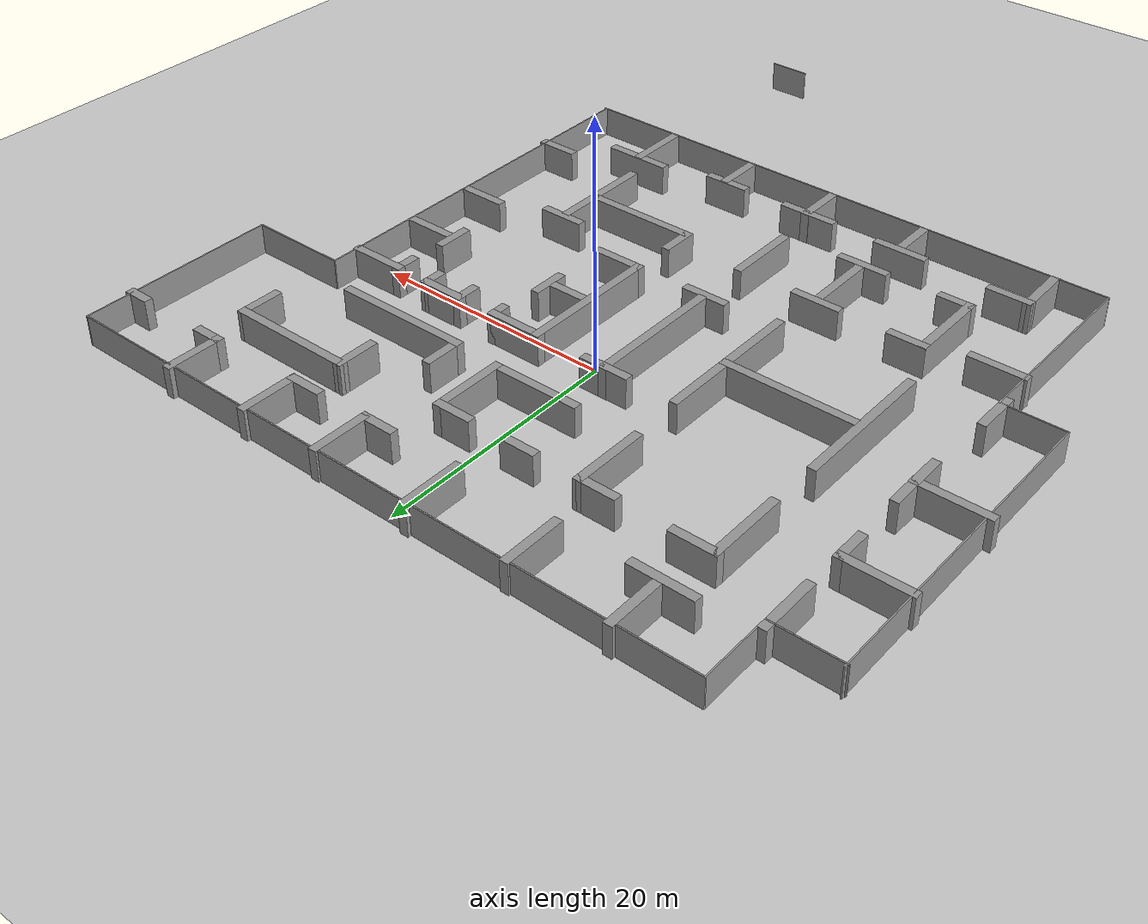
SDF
<?xml version='1.0' encoding='utf-8'?>
<sdf version="1.7">
  <world name="default">
    <light name="sun" type="directional">
      <cast_shadows>1</cast_shadows>
      <pose>0 0 10 0 -0 0</pose>
      <diffuse>0.8 0.8 0.8 1</diffuse>
      <specular>0.2 0.2 0.2 1</specular>
      <attenuation>
        <range>1000</range>
        <constant>0.9</constant>
        <linear>0.01</linear>
        <quadratic>0.001</quadratic>
      </attenuation>
      <direction>-0.5 0.1 -0.9</direction>
      <spot>
        <inner_angle>0</inner_angle>
        <outer_angle>0</outer_angle>
        <falloff>0</falloff>
      </spot>
    </light>
    <model name="ground_plane">
      <static>1</static>
      <link name="Wall_split_y">
  <collision name="Wall_split_y_Collision">
    <geometry>
      <box>
        <size>1 100 2.5</size>
      </box>
    </geometry>
    <pose>4.0 0 1.25 0 -0 0</pose>
    <max_contacts>10</max_contacts>
    <surface>
      <contact>
        <ode />
      </contact>
      <bounce />
      <friction>
        <torsional>
          <ode />
        </torsional>
        <ode />
      </friction>
    </surface>
  </collision>

  <visual name="Wall_split_y_Visual">
    <pose>4.0 0 1.25 0 -0 0</pose>
    <geometry>
      <box>
        <size>1 100 2.5</size>
      </box>
    </geometry>
    <material>
      <script>
        <uri>file://media/materials/scripts/gazebo.material</uri>
        <name>Gazebo/Grey</name>
      </script>
      <ambient>1 1 1 1</ambient>
    </material>
    <meta>
      <layer>0</layer>
    </meta>
  </visual>

  <pose>0 0 0 0 -0 0</pose>
  <self_collide>0</self_collide>
  <enable_wind>0</enable_wind>
  <kinematic>0</kinematic>
</link>
      <link name="link">
        <collision name="collision">
          <geometry>
            <plane>
              <normal>0 0 1</normal>
              <size>100 100</size>
            </plane>
          </geometry>
          <surface>
            <friction>
              <ode>
                <mu>100</mu>
                <mu2>50</mu2>
              </ode>
              <torsional>
                <ode />
              </torsional>
            </friction>
            <contact>
              <ode />
            </contact>
            <bounce />
          </surface>
          <max_contacts>10</max_contacts>
        </collision>
        <visual name="visual">
          <cast_shadows>0</cast_shadows>
          <geometry>
            <plane>
              <normal>0 0 1</normal>
              <size>100 100</size>
            </plane>
          </geometry>
          <material>
            <script>
              <uri>file://media/materials/scripts/gazebo.material</uri>
              <name>Gazebo/Grey</name>
            </script>
          </material>
        </visual>
        <self_collide>0</self_collide>
        <enable_wind>0</enable_wind>
        <kinematic>0</kinematic>
      </link>
    </model>
    <gravity>0 0 -9.8</gravity>
    <magnetic_field>6e-06 2.3e-05 -4.2e-05</magnetic_field>
    <atmosphere type="adiabatic" />
    <physics type="ode">
      <max_step_size>0.001</max_step_size>
      <real_time_factor>1</real_time_factor>
      <real_time_update_rate>1000</real_time_update_rate>
    </physics>
    <scene>
      <ambient>0.4 0.4 0.4 1</ambient>
      <background>0.7 0.7 0.7 1</background>
      <shadows>1</shadows>
    </scene>
    <wind />
    <spherical_coordinates>
      <surface_model>EARTH_WGS84</surface_model>
      <latitude_deg>0</latitude_deg>
      <longitude_deg>0</longitude_deg>
      <elevation>0</elevation>
      <heading_deg>0</heading_deg>
    </spherical_coordinates>
    <model name="map8">
      <pose>-0.03691 -11.806 0 0 -0 0</pose>
      <link name="Wall_0">
        <collision name="Wall_0_Collision">
          <geometry>
            <box>
              <size>26.6 0.105 2.5</size>
            </box>
          </geometry>
          <pose>0 0 1.25 0 -0 0</pose>
          <max_contacts>10</max_contacts>
          <surface>
            <contact>
              <ode />
            </contact>
            <bounce />
            <friction>
              <torsional>
                <ode />
              </torsional>
              <ode />
            </friction>
          </surface>
        </collision>
        <visual name="Wall_0_Visual">
          <pose>0 0 1.25 0 -0 0</pose>
          <geometry>
            <box>
              <size>26.6 0.105 2.5</size>
            </box>
          </geometry>
          <material>
            <script>
              <uri>file://media/materials/scripts/gazebo.material</uri>
              <name>Gazebo/Grey</name>
            </script>
            <ambient>1 1 1 1</ambient>
          </material>
          <meta>
            <layer>0</layer>
          </meta>
        </visual>
        <pose>-29.80348 13.45694 0 0 0 -1.5708</pose>
        <self_collide>0</self_collide>
        <enable_wind>0</enable_wind>
        <kinematic>0</kinematic>
      </link>
      <link name="Wall_1">
        <collision name="Wall_1_Collision">
          <geometry>
            <box>
              <size>5.075 0.105 2.5</size>
            </box>
          </geometry>
          <pose>0 0 1.25 0 -0 0</pose>
          <max_contacts>10</max_contacts>
          <surface>
            <contact>
              <ode />
            </contact>
            <bounce />
            <friction>
              <torsional>
                <ode />
              </torsional>
              <ode />
            </friction>
          </surface>
        </collision>
        <visual name="Wall_1_Visual">
          <pose>0 0 1.25 0 -0 0</pose>
          <geometry>
            <box>
              <size>5.075 0.105 2.5</size>
            </box>
          </geometry>
          <material>
            <script>
              <uri>file://media/materials/scripts/gazebo.material</uri>
              <name>Gazebo/Grey</name>
            </script>
            <ambient>1 1 1 1</ambient>
          </material>
          <meta>
            <layer>0</layer>
          </meta>
        </visual>
        <pose>-27.31848 0.209474 0 0 0 0</pose>
        <self_collide>0</self_collide>
        <enable_wind>0</enable_wind>
        <kinematic>0</kinematic>
      </link>
      <link name="Wall_100">
        <collision name="Wall_100_Collision">
          <geometry>
            <box>
              <size>5.495042 0.7 2.5</size>
            </box>
          </geometry>
          <pose>0 0 1.25 0 -0 0</pose>
          <max_contacts>10</max_contacts>
          <surface>
            <contact>
              <ode />
            </contact>
            <bounce />
            <friction>
              <torsional>
                <ode />
              </torsional>
              <ode />
            </friction>
          </surface>
        </collision>
        <visual name="Wall_100_Visual">
          <pose>0 0 1.25 0 -0 0</pose>
          <geometry>
            <box>
              <size>5.495042 0.7 2.5</size>
            </box>
          </geometry>
          <material>
            <script>
              <uri>file://media/materials/scripts/gazebo.material</uri>
              <name>Gazebo/Grey</name>
            </script>
            <ambient>1 1 1 1</ambient>
          </material>
          <meta>
            <layer>0</layer>
          </meta>
        </visual>
        <pose>14.28707 -11.01093 0 0 0 0</pose>
        <self_collide>0</self_collide>
        <enable_wind>0</enable_wind>
        <kinematic>0</kinematic>
      </link>
      <link name="Wall_102">
        <collision name="Wall_102_Collision">
          <geometry>
            <box>
              <size>5.145 0.7 2.5</size>
            </box>
          </geometry>
          <pose>0 0 1.25 0 -0 0</pose>
          <max_contacts>10</max_contacts>
          <surface>
            <contact>
              <ode />
            </contact>
            <bounce />
            <friction>
              <torsional>
                <ode />
              </torsional>
              <ode />
            </friction>
          </surface>
        </collision>
        <visual name="Wall_102_Visual">
          <pose>0 0 1.25 0 -0 0</pose>
          <geometry>
            <box>
              <size>5.145 0.7 2.5</size>
            </box>
          </geometry>
          <material>
            <script>
              <uri>file://media/materials/scripts/gazebo.material</uri>
              <name>Gazebo/Grey</name>
            </script>
            <ambient>1 1 1 1</ambient>
          </material>
          <meta>
            <layer>0</layer>
          </meta>
        </visual>
        <pose>14.22071 -13.33388 0 0 0 -1.5708</pose>
        <self_collide>0</self_collide>
        <enable_wind>0</enable_wind>
        <kinematic>0</kinematic>
      </link>
      <link name="Wall_104">
        <collision name="Wall_104_Collision">
          <geometry>
            <box>
              <size>3.325 0.105 2.5</size>
            </box>
          </geometry>
          <pose>0 0 1.25 0 -0 0</pose>
          <max_contacts>10</max_contacts>
          <surface>
            <contact>
              <ode />
            </contact>
            <bounce />
            <friction>
              <torsional>
                <ode />
              </torsional>
              <ode />
            </friction>
          </surface>
        </collision>
        <visual name="Wall_104_Visual">
          <pose>0 0 1.25 0 -0 0</pose>
          <geometry>
            <box>
              <size>3.325 0.105 2.5</size>
            </box>
          </geometry>
          <material>
            <script>
              <uri>file://media/materials/scripts/gazebo.material</uri>
              <name>Gazebo/Grey</name>
            </script>
            <ambient>1 1 1 1</ambient>
          </material>
          <meta>
            <layer>0</layer>
          </meta>
        </visual>
        <pose>13.96444 -32.51283 0 0 0 0</pose>
        <self_collide>0</self_collide>
        <enable_wind>0</enable_wind>
        <kinematic>0</kinematic>
      </link>
      <link name="Wall_106">
        <collision name="Wall_106_Collision">
          <geometry>
            <box>
              <size>3.92 0.7 2.5</size>
            </box>
          </geometry>
          <pose>0 0 1.25 0 -0 0</pose>
          <max_contacts>10</max_contacts>
          <surface>
            <contact>
              <ode />
            </contact>
            <bounce />
            <friction>
              <torsional>
                <ode />
              </torsional>
              <ode />
            </friction>
          </surface>
        </collision>
        <visual name="Wall_106_Visual">
          <pose>0 0 1.25 0 -0 0</pose>
          <geometry>
            <box>
              <size>3.92 0.7 2.5</size>
            </box>
          </geometry>
          <material>
            <script>
              <uri>file://media/materials/scripts/gazebo.material</uri>
              <name>Gazebo/Grey</name>
            </script>
            <ambient>1 1 1 1</ambient>
          </material>
          <meta>
            <layer>0</layer>
          </meta>
        </visual>
        <pose>6.376062 -13.98369 0 0 0 -1.5708</pose>
        <self_collide>0</self_collide>
        <enable_wind>0</enable_wind>
        <kinematic>0</kinematic>
      </link>
      <link name="Wall_108">
        <collision name="Wall_108_Collision">
          <geometry>
            <box>
              <size>3.744853 0.7 2.5</size>
            </box>
          </geometry>
          <pose>0 0 1.25 0 -0 0</pose>
          <max_contacts>10</max_contacts>
          <surface>
            <contact>
              <ode />
            </contact>
            <bounce />
            <friction>
              <torsional>
                <ode />
              </torsional>
              <ode />
            </friction>
          </surface>
        </collision>
        <visual name="Wall_108_Visual">
          <pose>0 0 1.25 0 -0 0</pose>
          <geometry>
            <box>
              <size>3.744853 0.7 2.5</size>
            </box>
          </geometry>
          <material>
            <script>
              <uri>file://media/materials/scripts/gazebo.material</uri>
              <name>Gazebo/Grey</name>
            </script>
            <ambient>1 1 1 1</ambient>
          </material>
          <meta>
            <layer>0</layer>
          </meta>
        </visual>
        <pose>6.167042 -12.22963 0 0 0 0</pose>
        <self_collide>0</self_collide>
        <enable_wind>0</enable_wind>
        <kinematic>0</kinematic>
      </link>
      <link name="Wall_110">
        <collision name="Wall_110_Collision">
          <geometry>
            <box>
              <size>3.395147 0.7 2.5</size>
            </box>
          </geometry>
          <pose>0 0 1.25 0 -0 0</pose>
          <max_contacts>10</max_contacts>
          <surface>
            <contact>
              <ode />
            </contact>
            <bounce />
            <friction>
              <torsional>
                <ode />
              </torsional>
              <ode />
            </friction>
          </surface>
        </collision>
        <visual name="Wall_110_Visual">
          <pose>0 0 1.25 0 -0 0</pose>
          <geometry>
            <box>
              <size>3.395147 0.7 2.5</size>
            </box>
          </geometry>
          <material>
            <script>
              <uri>file://media/materials/scripts/gazebo.material</uri>
              <name>Gazebo/Grey</name>
            </script>
            <ambient>1 1 1 1</ambient>
          </material>
          <meta>
            <layer>0</layer>
          </meta>
        </visual>
        <pose>20.44357 -8.03873 0 0 0 3.14159</pose>
        <self_collide>0</self_collide>
        <enable_wind>0</enable_wind>
        <kinematic>0</kinematic>
      </link>
      <link name="Wall_112">
        <collision name="Wall_112_Collision">
          <geometry>
            <box>
              <size>3.92 0.7 2.5</size>
            </box>
          </geometry>
          <pose>0 0 1.25 0 -0 0</pose>
          <max_contacts>10</max_contacts>
          <surface>
            <contact>
              <ode />
            </contact>
            <bounce />
            <friction>
              <torsional>
                <ode />
              </torsional>
              <ode />
            </friction>
          </surface>
        </collision>
        <visual name="Wall_112_Visual">
          <pose>0 0 1.25 0 -0 0</pose>
          <geometry>
            <box>
              <size>3.92 0.7 2.5</size>
            </box>
          </geometry>
          <material>
            <script>
              <uri>file://media/materials/scripts/gazebo.material</uri>
              <name>Gazebo/Grey</name>
            </script>
            <ambient>1 1 1 1</ambient>
          </material>
          <meta>
            <layer>0</layer>
          </meta>
        </visual>
        <pose>19.79712 1.792875 0 0 0 3.14159</pose>
        <self_collide>0</self_collide>
        <enable_wind>0</enable_wind>
        <kinematic>0</kinematic>
      </link>
      <link name="Wall_114">
        <collision name="Wall_114_Collision">
          <geometry>
            <box>
              <size>3.045343 0.7 2.5</size>
            </box>
          </geometry>
          <pose>0 0 1.25 0 -0 0</pose>
          <max_contacts>10</max_contacts>
          <surface>
            <contact>
              <ode />
            </contact>
            <bounce />
            <friction>
              <torsional>
                <ode />
              </torsional>
              <ode />
            </friction>
          </surface>
        </collision>
        <visual name="Wall_114_Visual">
          <pose>0 0 1.25 0 -0 0</pose>
          <geometry>
            <box>
              <size>3.045343 0.7 2.5</size>
            </box>
          </geometry>
          <material>
            <script>
              <uri>file://media/materials/scripts/gazebo.material</uri>
              <name>Gazebo/Grey</name>
            </script>
            <ambient>1 1 1 1</ambient>
          </material>
          <meta>
            <layer>0</layer>
          </meta>
        </visual>
        <pose>17.32297 7.93037 0 0 0 -1.5708</pose>
        <self_collide>0</self_collide>
        <enable_wind>0</enable_wind>
        <kinematic>0</kinematic>
      </link>
      <link name="Wall_116">
        <collision name="Wall_116_Collision">
          <geometry>
            <box>
              <size>4.55 0.7 2.5</size>
            </box>
          </geometry>
          <pose>0 0 1.25 0 -0 0</pose>
          <max_contacts>10</max_contacts>
          <surface>
            <contact>
              <ode />
            </contact>
            <bounce />
            <friction>
              <torsional>
                <ode />
              </torsional>
              <ode />
            </friction>
          </surface>
        </collision>
        <visual name="Wall_116_Visual">
          <pose>0 0 1.25 0 -0 0</pose>
          <geometry>
            <box>
              <size>4.55 0.7 2.5</size>
            </box>
          </geometry>
          <material>
            <script>
              <uri>file://media/materials/scripts/gazebo.material</uri>
              <name>Gazebo/Grey</name>
            </script>
            <ambient>1 1 1 1</ambient>
          </material>
          <meta>
            <layer>0</layer>
          </meta>
        </visual>
        <pose>19.44957 7.89537 0 0 0 0</pose>
        <self_collide>0</self_collide>
        <enable_wind>0</enable_wind>
        <kinematic>0</kinematic>
      </link>
      <link name="Wall_118">
        <collision name="Wall_118_Collision">
          <geometry>
            <box>
              <size>2.170014 0.7 2.5</size>
            </box>
          </geometry>
          <pose>0 0 1.25 0 -0 0</pose>
          <max_contacts>10</max_contacts>
          <surface>
            <contact>
              <ode />
            </contact>
            <bounce />
            <friction>
              <torsional>
                <ode />
              </torsional>
              <ode />
            </friction>
          </surface>
        </collision>
        <visual name="Wall_118_Visual">
          <pose>0 0 1.25 0 -0 0</pose>
          <geometry>
            <box>
              <size>2.170014 0.7 2.5</size>
            </box>
          </geometry>
          <material>
            <script>
              <uri>file://media/materials/scripts/gazebo.material</uri>
              <name>Gazebo/Grey</name>
            </script>
            <ambient>1 1 1 1</ambient>
          </material>
          <meta>
            <layer>0</layer>
          </meta>
        </visual>
        <pose>11.31802 12.88987 0 0 0 1.56841</pose>
        <self_collide>0</self_collide>
        <enable_wind>0</enable_wind>
        <kinematic>0</kinematic>
      </link>
      <link name="Wall_119">
        <collision name="Wall_119_Collision">
          <geometry>
            <box>
              <size>3.924207 0.7 2.5</size>
            </box>
          </geometry>
          <pose>0 0 1.25 0 -0 0</pose>
          <max_contacts>10</max_contacts>
          <surface>
            <contact>
              <ode />
            </contact>
            <bounce />
            <friction>
              <torsional>
                <ode />
              </torsional>
              <ode />
            </friction>
          </surface>
        </collision>
        <visual name="Wall_119_Visual">
          <pose>0 0 1.25 0 -0 0</pose>
          <geometry>
            <box>
              <size>3.924207 0.7 2.5</size>
            </box>
          </geometry>
          <material>
            <script>
              <uri>file://media/materials/scripts/gazebo.material</uri>
              <name>Gazebo/Grey</name>
            </script>
            <ambient>1 1 1 1</ambient>
          </material>
          <meta>
            <layer>0</layer>
          </meta>
        </visual>
        <pose>12.93187 13.62102 0 0 0 -0.002388</pose>
        <self_collide>0</self_collide>
        <enable_wind>0</enable_wind>
        <kinematic>0</kinematic>
      </link>
      <link name="Wall_120">
        <collision name="Wall_120_Collision">
          <geometry>
            <box>
              <size>1.994965 0.7 2.5</size>
            </box>
          </geometry>
          <pose>0 0 1.25 0 -0 0</pose>
          <max_contacts>10</max_contacts>
          <surface>
            <contact>
              <ode />
            </contact>
            <bounce />
            <friction>
              <torsional>
                <ode />
              </torsional>
              <ode />
            </friction>
          </surface>
        </collision>
        <visual name="Wall_120_Visual">
          <pose>0 0 1.25 0 -0 0</pose>
          <geometry>
            <box>
              <size>1.994965 0.7 2.5</size>
            </box>
          </geometry>
          <material>
            <script>
              <uri>file://media/materials/scripts/gazebo.material</uri>
              <name>Gazebo/Grey</name>
            </script>
            <ambient>1 1 1 1</ambient>
          </material>
          <meta>
            <layer>0</layer>
          </meta>
        </visual>
        <pose>14.54187 12.96967 0 0 0 -1.57404</pose>
        <self_collide>0</self_collide>
        <enable_wind>0</enable_wind>
        <kinematic>0</kinematic>
      </link>
      <link name="Wall_122">
        <collision name="Wall_122_Collision">
          <geometry>
            <box>
              <size>2.170014 0.7 2.5</size>
            </box>
          </geometry>
          <pose>0 0 1.25 0 -0 0</pose>
          <max_contacts>10</max_contacts>
          <surface>
            <contact>
              <ode />
            </contact>
            <bounce />
            <friction>
              <torsional>
                <ode />
              </torsional>
              <ode />
            </friction>
          </surface>
        </collision>
        <visual name="Wall_122_Visual">
          <pose>0 0 1.25 0 -0 0</pose>
          <geometry>
            <box>
              <size>2.170014 0.7 2.5</size>
            </box>
          </geometry>
          <material>
            <script>
              <uri>file://media/materials/scripts/gazebo.material</uri>
              <name>Gazebo/Grey</name>
            </script>
            <ambient>1 1 1 1</ambient>
          </material>
          <meta>
            <layer>0</layer>
          </meta>
        </visual>
        <pose>17.54207 12.81987 0 0 0 1.5708</pose>
        <self_collide>0</self_collide>
        <enable_wind>0</enable_wind>
        <kinematic>0</kinematic>
      </link>
      <link name="Wall_123">
        <collision name="Wall_123_Collision">
          <geometry>
            <box>
              <size>4.795196 0.7 2.5</size>
            </box>
          </geometry>
          <pose>0 0 1.25 0 -0 0</pose>
          <max_contacts>10</max_contacts>
          <surface>
            <contact>
              <ode />
            </contact>
            <bounce />
            <friction>
              <torsional>
                <ode />
              </torsional>
              <ode />
            </friction>
          </surface>
        </collision>
        <visual name="Wall_123_Visual">
          <pose>0 0 1.25 0 -0 0</pose>
          <geometry>
            <box>
              <size>4.795196 0.7 2.5</size>
            </box>
          </geometry>
          <material>
            <script>
              <uri>file://media/materials/scripts/gazebo.material</uri>
              <name>Gazebo/Grey</name>
            </script>
            <ambient>1 1 1 1</ambient>
          </material>
          <meta>
            <layer>0</layer>
          </meta>
        </visual>
        <pose>19.58957 13.55487 0 0 0 0</pose>
        <self_collide>0</self_collide>
        <enable_wind>0</enable_wind>
        <kinematic>0</kinematic>
      </link>
      <link name="Wall_125">
        <collision name="Wall_125_Collision">
          <geometry>
            <box>
              <size>4.55 0.7 2.5</size>
            </box>
          </geometry>
          <pose>0 0 1.25 0 -0 0</pose>
          <max_contacts>10</max_contacts>
          <surface>
            <contact>
              <ode />
            </contact>
            <bounce />
            <friction>
              <torsional>
                <ode />
              </torsional>
              <ode />
            </friction>
          </surface>
        </collision>
        <visual name="Wall_125_Visual">
          <pose>0 0 1.25 0 -0 0</pose>
          <geometry>
            <box>
              <size>4.55 0.7 2.5</size>
            </box>
          </geometry>
          <material>
            <script>
              <uri>file://media/materials/scripts/gazebo.material</uri>
              <name>Gazebo/Grey</name>
            </script>
            <ambient>1 1 1 1</ambient>
          </material>
          <meta>
            <layer>0</layer>
          </meta>
        </visual>
        <pose>-17.88633 30.17357 0 0 0 -1.5708</pose>
        <self_collide>0</self_collide>
        <enable_wind>0</enable_wind>
        <kinematic>0</kinematic>
      </link>
      <link name="Wall_128">
        <collision name="Wall_128_Collision">
          <geometry>
            <box>
              <size>5.144832 0.7 2.5</size>
            </box>
          </geometry>
          <pose>0 0 1.25 0 -0 0</pose>
          <max_contacts>10</max_contacts>
          <surface>
            <contact>
              <ode />
            </contact>
            <bounce />
            <friction>
              <torsional>
                <ode />
              </torsional>
              <ode />
            </friction>
          </surface>
        </collision>
        <visual name="Wall_128_Visual">
          <pose>0 0 1.25 0 -0 0</pose>
          <geometry>
            <box>
              <size>5.144832 0.7 2.5</size>
            </box>
          </geometry>
          <material>
            <script>
              <uri>file://media/materials/scripts/gazebo.material</uri>
              <name>Gazebo/Grey</name>
            </script>
            <ambient>1 1 1 1</ambient>
          </material>
          <meta>
            <layer>0</layer>
          </meta>
        </visual>
        <pose>-18.02283 27.55067 0 0 0 0</pose>
        <self_collide>0</self_collide>
        <enable_wind>0</enable_wind>
        <kinematic>0</kinematic>
      </link>
      <link name="Wall_13">
        <collision name="Wall_13_Collision">
          <geometry>
            <box>
              <size>4.97 0.7 2.5</size>
            </box>
          </geometry>
          <pose>0 0 1.25 0 -0 0</pose>
          <max_contacts>10</max_contacts>
          <surface>
            <contact>
              <ode />
            </contact>
            <bounce />
            <friction>
              <torsional>
                <ode />
              </torsional>
              <ode />
            </friction>
          </surface>
        </collision>
        <visual name="Wall_13_Visual">
          <pose>0 0 1.25 0 -0 0</pose>
          <geometry>
            <box>
              <size>4.97 0.7 2.5</size>
            </box>
          </geometry>
          <material>
            <script>
              <uri>file://media/materials/scripts/gazebo.material</uri>
              <name>Gazebo/Grey</name>
            </script>
            <ambient>1 1 1 1</ambient>
          </material>
          <meta>
            <layer>0</layer>
          </meta>
        </visual>
        <pose>-24.71105 24.76964 0 0 0 -1.5708</pose>
        <self_collide>0</self_collide>
        <enable_wind>0</enable_wind>
        <kinematic>0</kinematic>
      </link>
      <link name="Wall_130">
        <collision name="Wall_130_Collision">
          <geometry>
            <box>
              <size>4.970042 0.7 2.5</size>
            </box>
          </geometry>
          <pose>0 0 1.25 0 -0 0</pose>
          <max_contacts>10</max_contacts>
          <surface>
            <contact>
              <ode />
            </contact>
            <bounce />
            <friction>
              <torsional>
                <ode />
              </torsional>
              <ode />
            </friction>
          </surface>
        </collision>
        <visual name="Wall_130_Visual">
          <pose>0 0 1.25 0 -0 0</pose>
          <geometry>
            <box>
              <size>4.970042 0.7 2.5</size>
            </box>
          </geometry>
          <material>
            <script>
              <uri>file://media/materials/scripts/gazebo.material</uri>
              <name>Gazebo/Grey</name>
            </script>
            <ambient>1 1 1 1</ambient>
          </material>
          <meta>
            <layer>0</layer>
          </meta>
        </visual>
        <pose>-9.95673 29.84317 0 0 0 -1.5708</pose>
        <self_collide>0</self_collide>
        <enable_wind>0</enable_wind>
        <kinematic>0</kinematic>
      </link>
      <link name="Wall_132">
        <collision name="Wall_132_Collision">
          <geometry>
            <box>
              <size>5.145336 0.7 2.5</size>
            </box>
          </geometry>
          <pose>0 0 1.25 0 -0 0</pose>
          <max_contacts>10</max_contacts>
          <surface>
            <contact>
              <ode />
            </contact>
            <bounce />
            <friction>
              <torsional>
                <ode />
              </torsional>
              <ode />
            </friction>
          </surface>
        </collision>
        <visual name="Wall_132_Visual">
          <pose>0 0 1.25 0 -0 0</pose>
          <geometry>
            <box>
              <size>5.145336 0.7 2.5</size>
            </box>
          </geometry>
          <material>
            <script>
              <uri>file://media/materials/scripts/gazebo.material</uri>
              <name>Gazebo/Grey</name>
            </script>
            <ambient>1 1 1 1</ambient>
          </material>
          <meta>
            <layer>0</layer>
          </meta>
        </visual>
        <pose>-1.737358 29.88307 0 0 0 -1.5708</pose>
        <self_collide>0</self_collide>
        <enable_wind>0</enable_wind>
        <kinematic>0</kinematic>
      </link>
      <link name="Wall_134">
        <collision name="Wall_134_Collision">
          <geometry>
            <box>
              <size>4.97 0.7 2.5</size>
            </box>
          </geometry>
          <pose>0 0 1.25 0 -0 0</pose>
          <max_contacts>10</max_contacts>
          <surface>
            <contact>
              <ode />
            </contact>
            <bounce />
            <friction>
              <torsional>
                <ode />
              </torsional>
              <ode />
            </friction>
          </surface>
        </collision>
        <visual name="Wall_134_Visual">
          <pose>0 0 1.25 0 -0 0</pose>
          <geometry>
            <box>
              <size>4.97 0.7 2.5</size>
            </box>
          </geometry>
          <material>
            <script>
              <uri>file://media/materials/scripts/gazebo.material</uri>
              <name>Gazebo/Grey</name>
            </script>
            <ambient>1 1 1 1</ambient>
          </material>
          <meta>
            <layer>0</layer>
          </meta>
        </visual>
        <pose>6.388942 29.85857 0 0 0 -1.5708</pose>
        <self_collide>0</self_collide>
        <enable_wind>0</enable_wind>
        <kinematic>0</kinematic>
      </link>
      <link name="Wall_135">
        <collision name="Wall_135_Collision">
          <geometry>
            <box>
              <size>3.044909 0.7 2.5</size>
            </box>
          </geometry>
          <pose>0 0 1.25 0 -0 0</pose>
          <max_contacts>10</max_contacts>
          <surface>
            <contact>
              <ode />
            </contact>
            <bounce />
            <friction>
              <torsional>
                <ode />
              </torsional>
              <ode />
            </friction>
          </surface>
        </collision>
        <visual name="Wall_135_Visual">
          <pose>0 0 1.25 0 -0 0</pose>
          <geometry>
            <box>
              <size>3.044909 0.7 2.5</size>
            </box>
          </geometry>
          <material>
            <script>
              <uri>file://media/materials/scripts/gazebo.material</uri>
              <name>Gazebo/Grey</name>
            </script>
            <ambient>1 1 1 1</ambient>
          </material>
          <meta>
            <layer>0</layer>
          </meta>
        </visual>
        <pose>5.216442 27.72357 0 0 0 3.14159</pose>
        <self_collide>0</self_collide>
        <enable_wind>0</enable_wind>
        <kinematic>0</kinematic>
      </link>
      <link name="Wall_138">
        <collision name="Wall_138_Collision">
          <geometry>
            <box>
              <size>2.170014 0.7 2.5</size>
            </box>
          </geometry>
          <pose>0 0 1.25 0 -0 0</pose>
          <max_contacts>10</max_contacts>
          <surface>
            <contact>
              <ode />
            </contact>
            <bounce />
            <friction>
              <torsional>
                <ode />
              </torsional>
              <ode />
            </friction>
          </surface>
        </collision>
        <visual name="Wall_138_Visual">
          <pose>0 0 1.25 0 -0 0</pose>
          <geometry>
            <box>
              <size>2.170014 0.7 2.5</size>
            </box>
          </geometry>
          <material>
            <script>
              <uri>file://media/materials/scripts/gazebo.material</uri>
              <name>Gazebo/Grey</name>
            </script>
            <ambient>1 1 1 1</ambient>
          </material>
          <meta>
            <layer>0</layer>
          </meta>
        </visual>
        <pose>29.27127 28.11557 0 0 0 3.14159</pose>
        <self_collide>0</self_collide>
        <enable_wind>0</enable_wind>
        <kinematic>0</kinematic>
      </link>
      <link name="Wall_140">
        <collision name="Wall_140_Collision">
          <geometry>
            <box>
              <size>2.870301 0.7 2.5</size>
            </box>
          </geometry>
          <pose>0 0 1.25 0 -0 0</pose>
          <max_contacts>10</max_contacts>
          <surface>
            <contact>
              <ode />
            </contact>
            <bounce />
            <friction>
              <torsional>
                <ode />
              </torsional>
              <ode />
            </friction>
          </surface>
        </collision>
        <visual name="Wall_140_Visual">
          <pose>0 0 1.25 0 -0 0</pose>
          <geometry>
            <box>
              <size>2.870301 0.7 2.5</size>
            </box>
          </geometry>
          <material>
            <script>
              <uri>file://media/materials/scripts/gazebo.material</uri>
              <name>Gazebo/Grey</name>
            </script>
            <ambient>1 1 1 1</ambient>
          </material>
          <meta>
            <layer>0</layer>
          </meta>
        </visual>
        <pose>-3.418758 23.59707 0 0 0 0</pose>
        <self_collide>0</self_collide>
        <enable_wind>0</enable_wind>
        <kinematic>0</kinematic>
      </link>
      <link name="Wall_15">
        <collision name="Wall_15_Collision">
          <geometry>
            <box>
              <size>5.67 0.7 2.5</size>
            </box>
          </geometry>
          <pose>0 0 1.25 0 -0 0</pose>
          <max_contacts>10</max_contacts>
          <surface>
            <contact>
              <ode />
            </contact>
            <bounce />
            <friction>
              <torsional>
                <ode />
              </torsional>
              <ode />
            </friction>
          </surface>
        </collision>
        <visual name="Wall_15_Visual">
          <pose>0 0 1.25 0 -0 0</pose>
          <geometry>
            <box>
              <size>5.67 0.7 2.5</size>
            </box>
          </geometry>
          <material>
            <script>
              <uri>file://media/materials/scripts/gazebo.material</uri>
              <name>Gazebo/Grey</name>
            </script>
            <ambient>1 1 1 1</ambient>
          </material>
          <meta>
            <layer>0</layer>
          </meta>
        </visual>
        <pose>-27.27753 19.37257 0 0 0 0</pose>
        <self_collide>0</self_collide>
        <enable_wind>0</enable_wind>
        <kinematic>0</kinematic>
      </link>
      <link name="Wall_16">
        <collision name="Wall_16_Collision">
          <geometry>
            <box>
              <size>2.870294 0.7 2.5</size>
            </box>
          </geometry>
          <pose>0 0 1.25 0 -0 0</pose>
          <max_contacts>10</max_contacts>
          <surface>
            <contact>
              <ode />
            </contact>
            <bounce />
            <friction>
              <torsional>
                <ode />
              </torsional>
              <ode />
            </friction>
          </surface>
        </collision>
        <visual name="Wall_16_Visual">
          <pose>0 0 1.25 0 -0 0</pose>
          <geometry>
            <box>
              <size>2.870294 0.7 2.5</size>
            </box>
          </geometry>
          <material>
            <script>
              <uri>file://media/materials/scripts/gazebo.material</uri>
              <name>Gazebo/Grey</name>
            </script>
            <ambient>1 1 1 1</ambient>
          </material>
          <meta>
            <layer>0</layer>
          </meta>
        </visual>
        <pose>-24.79253 18.28757 0 0 0 -1.5708</pose>
        <self_collide>0</self_collide>
        <enable_wind>0</enable_wind>
        <kinematic>0</kinematic>
      </link>
      <link name="Wall_18">
        <collision name="Wall_18_Collision">
          <geometry>
            <box>
              <size>6.020189 0.7 2.5</size>
            </box>
          </geometry>
          <pose>0 0 1.25 0 -0 0</pose>
          <max_contacts>10</max_contacts>
          <surface>
            <contact>
              <ode />
            </contact>
            <bounce />
            <friction>
              <torsional>
                <ode />
              </torsional>
              <ode />
            </friction>
          </surface>
        </collision>
        <visual name="Wall_18_Visual">
          <pose>0 0 1.25 0 -0 0</pose>
          <geometry>
            <box>
              <size>6.020189 0.7 2.5</size>
            </box>
          </geometry>
          <material>
            <script>
              <uri>file://media/materials/scripts/gazebo.material</uri>
              <name>Gazebo/Grey</name>
            </script>
            <ambient>1 1 1 1</ambient>
          </material>
          <meta>
            <layer>0</layer>
          </meta>
        </visual>
        <pose>-27.34613 10.66807 0 0 0 0</pose>
        <self_collide>0</self_collide>
        <enable_wind>0</enable_wind>
        <kinematic>0</kinematic>
      </link>
      <link name="Wall_2">
        <collision name="Wall_2_Collision">
          <geometry>
            <box>
              <size>16.23762 0.105 2.5</size>
            </box>
          </geometry>
          <pose>0 0 1.25 0 -0 0</pose>
          <max_contacts>10</max_contacts>
          <surface>
            <contact>
              <ode />
            </contact>
            <bounce />
            <friction>
              <torsional>
                <ode />
              </torsional>
              <ode />
            </friction>
          </surface>
        </collision>
        <visual name="Wall_2_Visual">
          <pose>0 0 1.25 0 -0 0</pose>
          <geometry>
            <box>
              <size>16.23762 0.105 2.5</size>
            </box>
          </geometry>
          <material>
            <script>
              <uri>file://media/materials/scripts/gazebo.material</uri>
              <name>Gazebo/Grey</name>
            </script>
            <ambient>1 1 1 1</ambient>
          </material>
          <meta>
            <layer>0</layer>
          </meta>
        </visual>
        <pose>-24.86505 -7.85666 0 0 0 -1.57471</pose>
        <self_collide>0</self_collide>
        <enable_wind>0</enable_wind>
        <kinematic>0</kinematic>
      </link>
      <link name="Wall_20">
        <collision name="Wall_20_Collision">
          <geometry>
            <box>
              <size>5.144832 0.7 2.5</size>
            </box>
          </geometry>
          <pose>0 0 1.25 0 -0 0</pose>
          <max_contacts>10</max_contacts>
          <surface>
            <contact>
              <ode />
            </contact>
            <bounce />
            <friction>
              <torsional>
                <ode />
              </torsional>
              <ode />
            </friction>
          </surface>
        </collision>
        <visual name="Wall_20_Visual">
          <pose>0 0 1.25 0 -0 0</pose>
          <geometry>
            <box>
              <size>5.144832 0.7 2.5</size>
            </box>
          </geometry>
          <material>
            <script>
              <uri>file://media/materials/scripts/gazebo.material</uri>
              <name>Gazebo/Grey</name>
            </script>
            <ambient>1 1 1 1</ambient>
          </material>
          <meta>
            <layer>0</layer>
          </meta>
        </visual>
        <pose>-24.71063 10.63657 0 0 0 -1.5708</pose>
        <self_collide>0</self_collide>
        <enable_wind>0</enable_wind>
        <kinematic>0</kinematic>
      </link>
      <link name="Wall_22">
        <collision name="Wall_22_Collision">
          <geometry>
            <box>
              <size>12.14514 0.7 2.5</size>
            </box>
          </geometry>
          <pose>0 0 1.25 0 -0 0</pose>
          <max_contacts>10</max_contacts>
          <surface>
            <contact>
              <ode />
            </contact>
            <bounce />
            <friction>
              <torsional>
                <ode />
              </torsional>
              <ode />
            </friction>
          </surface>
        </collision>
        <visual name="Wall_22_Visual">
          <pose>0 0 1.25 0 -0 0</pose>
          <geometry>
            <box>
              <size>12.14514 0.7 2.5</size>
            </box>
          </geometry>
          <material>
            <script>
              <uri>file://media/materials/scripts/gazebo.material</uri>
              <name>Gazebo/Grey</name>
            </script>
            <ambient>1 1 1 1</ambient>
          </material>
          <meta>
            <layer>0</layer>
          </meta>
        </visual>
        <pose>-19.11063 7.74557 0 0 0 -1.5708</pose>
        <self_collide>0</self_collide>
        <enable_wind>0</enable_wind>
        <kinematic>0</kinematic>
      </link>
      <link name="Wall_24">
        <collision name="Wall_24_Collision">
          <geometry>
            <box>
              <size>10.85 0.7 2.5</size>
            </box>
          </geometry>
          <pose>0 0 1.25 0 -0 0</pose>
          <max_contacts>10</max_contacts>
          <surface>
            <contact>
              <ode />
            </contact>
            <bounce />
            <friction>
              <torsional>
                <ode />
              </torsional>
              <ode />
            </friction>
          </surface>
        </collision>
        <visual name="Wall_24_Visual">
          <pose>0 0 1.25 0 -0 0</pose>
          <geometry>
            <box>
              <size>10.85 0.7 2.5</size>
            </box>
          </geometry>
          <material>
            <script>
              <uri>file://media/materials/scripts/gazebo.material</uri>
              <name>Gazebo/Grey</name>
            </script>
            <ambient>1 1 1 1</ambient>
          </material>
          <meta>
            <layer>0</layer>
          </meta>
        </visual>
        <pose>-13.38673 7.98987 0 0 0 0</pose>
        <self_collide>0</self_collide>
        <enable_wind>0</enable_wind>
        <kinematic>0</kinematic>
      </link>
      <link name="Wall_26">
        <collision name="Wall_26_Collision">
          <geometry>
            <box>
              <size>12.49514 0.7 2.5</size>
            </box>
          </geometry>
          <pose>0 0 1.25 0 -0 0</pose>
          <max_contacts>10</max_contacts>
          <surface>
            <contact>
              <ode />
            </contact>
            <bounce />
            <friction>
              <torsional>
                <ode />
              </torsional>
              <ode />
            </friction>
          </surface>
        </collision>
        <visual name="Wall_26_Visual">
          <pose>0 0 1.25 0 -0 0</pose>
          <geometry>
            <box>
              <size>12.49514 0.7 2.5</size>
            </box>
          </geometry>
          <material>
            <script>
              <uri>file://media/materials/scripts/gazebo.material</uri>
              <name>Gazebo/Grey</name>
            </script>
            <ambient>1 1 1 1</ambient>
          </material>
          <meta>
            <layer>0</layer>
          </meta>
        </visual>
        <pose>-8.27533 7.63147 0 0 0 -1.5708</pose>
        <self_collide>0</self_collide>
        <enable_wind>0</enable_wind>
        <kinematic>0</kinematic>
      </link>
      <link name="Wall_28">
        <collision name="Wall_28_Collision">
          <geometry>
            <box>
              <size>3.745 0.7 2.5</size>
            </box>
          </geometry>
          <pose>0 0 1.25 0 -0 0</pose>
          <max_contacts>10</max_contacts>
          <surface>
            <contact>
              <ode />
            </contact>
            <bounce />
            <friction>
              <torsional>
                <ode />
              </torsional>
              <ode />
            </friction>
          </surface>
        </collision>
        <visual name="Wall_28_Visual">
          <pose>0 0 1.25 0 -0 0</pose>
          <geometry>
            <box>
              <size>3.745 0.7 2.5</size>
            </box>
          </geometry>
          <material>
            <script>
              <uri>file://media/materials/scripts/gazebo.material</uri>
              <name>Gazebo/Grey</name>
            </script>
            <ambient>1 1 1 1</ambient>
          </material>
          <meta>
            <layer>0</layer>
          </meta>
        </visual>
        <pose>-25.11082 1.220604 0 0 0 -1.5708</pose>
        <self_collide>0</self_collide>
        <enable_wind>0</enable_wind>
        <kinematic>0</kinematic>
      </link>
      <link name="Wall_3">
        <collision name="Wall_3_Collision">
          <geometry>
            <box>
              <size>46.9 0.105 2.5</size>
            </box>
          </geometry>
          <pose>0 0 1.25 0 -0 0</pose>
          <max_contacts>10</max_contacts>
          <surface>
            <contact>
              <ode />
            </contact>
            <bounce />
            <friction>
              <torsional>
                <ode />
              </torsional>
              <ode />
            </friction>
          </surface>
        </collision>
        <visual name="Wall_3_Visual">
          <pose>0 0 1.25 0 -0 0</pose>
          <geometry>
            <box>
              <size>46.9 0.105 2.5</size>
            </box>
          </geometry>
          <material>
            <script>
              <uri>file://media/materials/scripts/gazebo.material</uri>
              <name>Gazebo/Grey</name>
            </script>
            <ambient>1 1 1 1</ambient>
          </material>
          <meta>
            <layer>0</layer>
          </meta>
        </visual>
        <pose>-1.499064 -15.92276 0 0 0 0</pose>
        <self_collide>0</self_collide>
        <enable_wind>0</enable_wind>
        <kinematic>0</kinematic>
      </link>
      <link name="Wall_30">
        <collision name="Wall_30_Collision">
          <geometry>
            <box>
              <size>4.619671 0.7 2.5</size>
            </box>
          </geometry>
          <pose>0 0 1.25 0 -0 0</pose>
          <max_contacts>10</max_contacts>
          <surface>
            <contact>
              <ode />
            </contact>
            <bounce />
            <friction>
              <torsional>
                <ode />
              </torsional>
              <ode />
            </friction>
          </surface>
        </collision>
        <visual name="Wall_30_Visual">
          <pose>0 0 1.25 0 -0 0</pose>
          <geometry>
            <box>
              <size>4.619671 0.7 2.5</size>
            </box>
          </geometry>
          <material>
            <script>
              <uri>file://media/materials/scripts/gazebo.material</uri>
              <name>Gazebo/Grey</name>
            </script>
            <ambient>1 1 1 1</ambient>
          </material>
          <meta>
            <layer>0</layer>
          </meta>
        </visual>
        <pose>-22.81083 -3.453758 0 0 0 0</pose>
        <self_collide>0</self_collide>
        <enable_wind>0</enable_wind>
        <kinematic>0</kinematic>
      </link>
      <link name="Wall_32">
        <collision name="Wall_32_Collision">
          <geometry>
            <box>
              <size>3.745 0.7 2.5</size>
            </box>
          </geometry>
          <pose>0 0 1.25 0 -0 0</pose>
          <max_contacts>10</max_contacts>
          <surface>
            <contact>
              <ode />
            </contact>
            <bounce />
            <friction>
              <torsional>
                <ode />
              </torsional>
              <ode />
            </friction>
          </surface>
        </collision>
        <visual name="Wall_32_Visual">
          <pose>0 0 1.25 0 -0 0</pose>
          <geometry>
            <box>
              <size>3.745 0.7 2.5</size>
            </box>
          </geometry>
          <material>
            <script>
              <uri>file://media/materials/scripts/gazebo.material</uri>
              <name>Gazebo/Grey</name>
            </script>
            <ambient>1 1 1 1</ambient>
          </material>
          <meta>
            <layer>0</layer>
          </meta>
        </visual>
        <pose>-17.46773 23.75457 0 0 0 3.14159</pose>
        <self_collide>0</self_collide>
        <enable_wind>0</enable_wind>
        <kinematic>0</kinematic>
      </link>
      <link name="Wall_33">
        <collision name="Wall_33_Collision">
          <geometry>
            <box>
              <size>6.544685 0.7 2.5</size>
            </box>
          </geometry>
          <pose>0 0 1.25 0 -0 0</pose>
          <max_contacts>10</max_contacts>
          <surface>
            <contact>
              <ode />
            </contact>
            <bounce />
            <friction>
              <torsional>
                <ode />
              </torsional>
              <ode />
            </friction>
          </surface>
        </collision>
        <visual name="Wall_33_Visual">
          <pose>0 0 1.25 0 -0 0</pose>
          <geometry>
            <box>
              <size>6.544685 0.7 2.5</size>
            </box>
          </geometry>
          <material>
            <script>
              <uri>file://media/materials/scripts/gazebo.material</uri>
              <name>Gazebo/Grey</name>
            </script>
            <ambient>1 1 1 1</ambient>
          </material>
          <meta>
            <layer>0</layer>
          </meta>
        </visual>
        <pose>-18.99023 20.83207 0 0 0 -1.5708</pose>
        <self_collide>0</self_collide>
        <enable_wind>0</enable_wind>
        <kinematic>0</kinematic>
      </link>
      <link name="Wall_35">
        <collision name="Wall_35_Collision">
          <geometry>
            <box>
              <size>3.39486 0.7 2.5</size>
            </box>
          </geometry>
          <pose>0 0 1.25 0 -0 0</pose>
          <max_contacts>10</max_contacts>
          <surface>
            <contact>
              <ode />
            </contact>
            <bounce />
            <friction>
              <torsional>
                <ode />
              </torsional>
              <ode />
            </friction>
          </surface>
        </collision>
        <visual name="Wall_35_Visual">
          <pose>0 0 1.25 0 -0 0</pose>
          <geometry>
            <box>
              <size>3.39486 0.7 2.5</size>
            </box>
          </geometry>
          <material>
            <script>
              <uri>file://media/materials/scripts/gazebo.material</uri>
              <name>Gazebo/Grey</name>
            </script>
            <ambient>1 1 1 1</ambient>
          </material>
          <meta>
            <layer>0</layer>
          </meta>
        </visual>
        <pose>-9.82933 23.63347 0 0 0 0</pose>
        <self_collide>0</self_collide>
        <enable_wind>0</enable_wind>
        <kinematic>0</kinematic>
      </link>
      <link name="Wall_36">
        <collision name="Wall_36_Collision">
          <geometry>
            <box>
              <size>6.195357 0.7 2.5</size>
            </box>
          </geometry>
          <pose>0 0 1.25 0 -0 0</pose>
          <max_contacts>10</max_contacts>
          <surface>
            <contact>
              <ode />
            </contact>
            <bounce />
            <friction>
              <torsional>
                <ode />
              </torsional>
              <ode />
            </friction>
          </surface>
        </collision>
        <visual name="Wall_36_Visual">
          <pose>0 0 1.25 0 -0 0</pose>
          <geometry>
            <box>
              <size>6.195357 0.7 2.5</size>
            </box>
          </geometry>
          <material>
            <script>
              <uri>file://media/materials/scripts/gazebo.material</uri>
              <name>Gazebo/Grey</name>
            </script>
            <ambient>1 1 1 1</ambient>
          </material>
          <meta>
            <layer>0</layer>
          </meta>
        </visual>
        <pose>-8.49198 20.88597 0 0 0 -1.57449</pose>
        <self_collide>0</self_collide>
        <enable_wind>0</enable_wind>
        <kinematic>0</kinematic>
      </link>
      <link name="Wall_38">
        <collision name="Wall_38_Collision">
          <geometry>
            <box>
              <size>3.22 0.7 2.5</size>
            </box>
          </geometry>
          <pose>0 0 1.25 0 -0 0</pose>
          <max_contacts>10</max_contacts>
          <surface>
            <contact>
              <ode />
            </contact>
            <bounce />
            <friction>
              <torsional>
                <ode />
              </torsional>
              <ode />
            </friction>
          </surface>
        </collision>
        <visual name="Wall_38_Visual">
          <pose>0 0 1.25 0 -0 0</pose>
          <geometry>
            <box>
              <size>3.22 0.7 2.5</size>
            </box>
          </geometry>
          <material>
            <script>
              <uri>file://media/materials/scripts/gazebo.material</uri>
              <name>Gazebo/Grey</name>
            </script>
            <ambient>1 1 1 1</ambient>
          </material>
          <meta>
            <layer>0</layer>
          </meta>
        </visual>
        <pose>2.297442 23.63347 0 0 0 0</pose>
        <self_collide>0</self_collide>
        <enable_wind>0</enable_wind>
        <kinematic>0</kinematic>
      </link>
      <link name="Wall_39">
        <collision name="Wall_39_Collision">
          <geometry>
            <box>
              <size>6.195322 0.7 2.5</size>
            </box>
          </geometry>
          <pose>0 0 1.25 0 -0 0</pose>
          <max_contacts>10</max_contacts>
          <surface>
            <contact>
              <ode />
            </contact>
            <bounce />
            <friction>
              <torsional>
                <ode />
              </torsional>
              <ode />
            </friction>
          </surface>
        </collision>
        <visual name="Wall_39_Visual">
          <pose>0 0 1.25 0 -0 0</pose>
          <geometry>
            <box>
              <size>6.195322 0.7 2.5</size>
            </box>
          </geometry>
          <material>
            <script>
              <uri>file://media/materials/scripts/gazebo.material</uri>
              <name>Gazebo/Grey</name>
            </script>
            <ambient>1 1 1 1</ambient>
          </material>
          <meta>
            <layer>0</layer>
          </meta>
        </visual>
        <pose>3.557442 20.88597 0 0 0 -1.5708</pose>
        <self_collide>0</self_collide>
        <enable_wind>0</enable_wind>
        <kinematic>0</kinematic>
      </link>
      <link name="Wall_4">
        <collision name="Wall_4_Collision">
          <geometry>
            <box>
              <size>31.98727 0.105 2.5</size>
            </box>
          </geometry>
          <pose>0 0 1.25 0 -0 0</pose>
          <max_contacts>10</max_contacts>
          <surface>
            <contact>
              <ode />
            </contact>
            <bounce />
            <friction>
              <torsional>
                <ode />
              </torsional>
              <ode />
            </friction>
          </surface>
        </collision>
        <visual name="Wall_4_Visual">
          <pose>0 0 1.25 0 -0 0</pose>
          <geometry>
            <box>
              <size>31.98727 0.105 2.5</size>
            </box>
          </geometry>
          <material>
            <script>
              <uri>file://media/materials/scripts/gazebo.material</uri>
              <name>Gazebo/Grey</name>
            </script>
            <ambient>1 1 1 1</ambient>
          </material>
          <meta>
            <layer>0</layer>
          </meta>
        </visual>
        <pose>21.76153 0.018344 0 0 0 1.56923</pose>
        <self_collide>0</self_collide>
        <enable_wind>0</enable_wind>
        <kinematic>0</kinematic>
      </link>
      <link name="Wall_40">
        <collision name="Wall_40_Collision">
          <geometry>
            <box>
              <size>7.59493 0.7 2.5</size>
            </box>
          </geometry>
          <pose>0 0 1.25 0 -0 0</pose>
          <max_contacts>10</max_contacts>
          <surface>
            <contact>
              <ode />
            </contact>
            <bounce />
            <friction>
              <torsional>
                <ode />
              </torsional>
              <ode />
            </friction>
          </surface>
        </collision>
        <visual name="Wall_40_Visual">
          <pose>0 0 1.25 0 -0 0</pose>
          <geometry>
            <box>
              <size>7.59493 0.7 2.5</size>
            </box>
          </geometry>
          <material>
            <script>
              <uri>file://media/materials/scripts/gazebo.material</uri>
              <name>Gazebo/Grey</name>
            </script>
            <ambient>1 1 1 1</ambient>
          </material>
          <meta>
            <layer>0</layer>
          </meta>
        </visual>
        <pose>0.109944 18.13847 0 0 0 3.14159</pose>
        <self_collide>0</self_collide>
        <enable_wind>0</enable_wind>
        <kinematic>0</kinematic>
      </link>
      <link name="Wall_42">
        <collision name="Wall_42_Collision">
          <geometry>
            <box>
              <size>4.094762 0.7 2.5</size>
            </box>
          </geometry>
          <pose>0 0 1.25 0 -0 0</pose>
          <max_contacts>10</max_contacts>
          <surface>
            <contact>
              <ode />
            </contact>
            <bounce />
            <friction>
              <torsional>
                <ode />
              </torsional>
              <ode />
            </friction>
          </surface>
        </collision>
        <visual name="Wall_42_Visual">
          <pose>0 0 1.25 0 -0 0</pose>
          <geometry>
            <box>
              <size>4.094762 0.7 2.5</size>
            </box>
          </geometry>
          <material>
            <script>
              <uri>file://media/materials/scripts/gazebo.material</uri>
              <name>Gazebo/Grey</name>
            </script>
            <ambient>1 1 1 1</ambient>
          </material>
          <meta>
            <layer>0</layer>
          </meta>
        </visual>
        <pose>-2.256058 13.52897 0 0 0 0</pose>
        <self_collide>0</self_collide>
        <enable_wind>0</enable_wind>
        <kinematic>0</kinematic>
      </link>
      <link name="Wall_44">
        <collision name="Wall_44_Collision">
          <geometry>
            <box>
              <size>3.745 0.7 2.5</size>
            </box>
          </geometry>
          <pose>0 0 1.25 0 -0 0</pose>
          <max_contacts>10</max_contacts>
          <surface>
            <contact>
              <ode />
            </contact>
            <bounce />
            <friction>
              <torsional>
                <ode />
              </torsional>
              <ode />
            </friction>
          </surface>
        </collision>
        <visual name="Wall_44_Visual">
          <pose>0 0 1.25 0 -0 0</pose>
          <geometry>
            <box>
              <size>3.745 0.7 2.5</size>
            </box>
          </geometry>
          <material>
            <script>
              <uri>file://media/materials/scripts/gazebo.material</uri>
              <name>Gazebo/Grey</name>
            </script>
            <ambient>1 1 1 1</ambient>
          </material>
          <meta>
            <layer>0</layer>
          </meta>
        </visual>
        <pose>-2.248358 2.143792 0 0 0 0</pose>
        <self_collide>0</self_collide>
        <enable_wind>0</enable_wind>
        <kinematic>0</kinematic>
      </link>
      <link name="Wall_46">
        <collision name="Wall_46_Collision">
          <geometry>
            <box>
              <size>11.97014 0.7 2.5</size>
            </box>
          </geometry>
          <pose>0 0 1.25 0 -0 0</pose>
          <max_contacts>10</max_contacts>
          <surface>
            <contact>
              <ode />
            </contact>
            <bounce />
            <friction>
              <torsional>
                <ode />
              </torsional>
              <ode />
            </friction>
          </surface>
        </collision>
        <visual name="Wall_46_Visual">
          <pose>0 0 1.25 0 -0 0</pose>
          <geometry>
            <box>
              <size>11.97014 0.7 2.5</size>
            </box>
          </geometry>
          <material>
            <script>
              <uri>file://media/materials/scripts/gazebo.material</uri>
              <name>Gazebo/Grey</name>
            </script>
            <ambient>1 1 1 1</ambient>
          </material>
          <meta>
            <layer>0</layer>
          </meta>
        </visual>
        <pose>-2.188858 7.89397 0 0 0 -1.5708</pose>
        <self_collide>0</self_collide>
        <enable_wind>0</enable_wind>
        <kinematic>0</kinematic>
      </link>
      <link name="Wall_48">
        <collision name="Wall_48_Collision">
          <geometry>
            <box>
              <size>1.645 0.7 2.5</size>
            </box>
          </geometry>
          <pose>0 0 1.25 0 -0 0</pose>
          <max_contacts>10</max_contacts>
          <surface>
            <contact>
              <ode />
            </contact>
            <bounce />
            <friction>
              <torsional>
                <ode />
              </torsional>
              <ode />
            </friction>
          </surface>
        </collision>
        <visual name="Wall_48_Visual">
          <pose>0 0 1.25 0 -0 0</pose>
          <geometry>
            <box>
              <size>1.645 0.7 2.5</size>
            </box>
          </geometry>
          <material>
            <script>
              <uri>file://media/materials/scripts/gazebo.material</uri>
              <name>Gazebo/Grey</name>
            </script>
            <ambient>1 1 1 1</ambient>
          </material>
          <meta>
            <layer>0</layer>
          </meta>
        </visual>
        <pose>7.97657 13.08797 0 0 0 1.5708</pose>
        <self_collide>0</self_collide>
        <enable_wind>0</enable_wind>
        <kinematic>0</kinematic>
      </link>
      <link name="Wall_49">
        <collision name="Wall_49_Collision">
          <geometry>
            <box>
              <size>4.795 0.7 2.5</size>
            </box>
          </geometry>
          <pose>0 0 1.25 0 -0 0</pose>
          <max_contacts>10</max_contacts>
          <surface>
            <contact>
              <ode />
            </contact>
            <bounce />
            <friction>
              <torsional>
                <ode />
              </torsional>
              <ode />
            </friction>
          </surface>
        </collision>
        <visual name="Wall_49_Visual">
          <pose>0 0 1.25 0 -0 0</pose>
          <geometry>
            <box>
              <size>4.795 0.7 2.5</size>
            </box>
          </geometry>
          <material>
            <script>
              <uri>file://media/materials/scripts/gazebo.material</uri>
              <name>Gazebo/Grey</name>
            </script>
            <ambient>1 1 1 1</ambient>
          </material>
          <meta>
            <layer>0</layer>
          </meta>
        </visual>
        <pose>5.929042 13.56047 0 0 0 3.14159</pose>
        <self_collide>0</self_collide>
        <enable_wind>0</enable_wind>
        <kinematic>0</kinematic>
      </link>
      <link name="Wall_5">
        <collision name="Wall_5_Collision">
          <geometry>
            <box>
              <size>8.225 0.105 2.5</size>
            </box>
          </geometry>
          <pose>0 0 1.25 0 -0 0</pose>
          <max_contacts>10</max_contacts>
          <surface>
            <contact>
              <ode />
            </contact>
            <bounce />
            <friction>
              <torsional>
                <ode />
              </torsional>
              <ode />
            </friction>
          </surface>
        </collision>
        <visual name="Wall_5_Visual">
          <pose>0 0 1.25 0 -0 0</pose>
          <geometry>
            <box>
              <size>8.225 0.105 2.5</size>
            </box>
          </geometry>
          <material>
            <script>
              <uri>file://media/materials/scripts/gazebo.material</uri>
              <name>Gazebo/Grey</name>
            </script>
            <ambient>1 1 1 1</ambient>
          </material>
          <meta>
            <layer>0</layer>
          </meta>
        </visual>
        <pose>25.84652 15.95944 0 0 0 0</pose>
        <self_collide>0</self_collide>
        <enable_wind>0</enable_wind>
        <kinematic>0</kinematic>
      </link>
      <link name="Wall_50">
        <collision name="Wall_50_Collision">
          <geometry>
            <box>
              <size>11.96972 0.7 2.5</size>
            </box>
          </geometry>
          <pose>0 0 1.25 0 -0 0</pose>
          <max_contacts>10</max_contacts>
          <surface>
            <contact>
              <ode />
            </contact>
            <bounce />
            <friction>
              <torsional>
                <ode />
              </torsional>
              <ode />
            </friction>
          </surface>
        </collision>
        <visual name="Wall_50_Visual">
          <pose>0 0 1.25 0 -0 0</pose>
          <geometry>
            <box>
              <size>11.96972 0.7 2.5</size>
            </box>
          </geometry>
          <material>
            <script>
              <uri>file://media/materials/scripts/gazebo.material</uri>
              <name>Gazebo/Grey</name>
            </script>
            <ambient>1 1 1 1</ambient>
          </material>
          <meta>
            <layer>0</layer>
          </meta>
        </visual>
        <pose>3.881542 7.92547 0 0 0 -1.5708</pose>
        <self_collide>0</self_collide>
        <enable_wind>0</enable_wind>
        <kinematic>0</kinematic>
      </link>
      <link name="Wall_51">
        <collision name="Wall_51_Collision">
          <geometry>
            <box>
              <size>4.270098 0.7 2.5</size>
            </box>
          </geometry>
          <pose>0 0 1.25 0 -0 0</pose>
          <max_contacts>10</max_contacts>
          <surface>
            <contact>
              <ode />
            </contact>
            <bounce />
            <friction>
              <torsional>
                <ode />
              </torsional>
              <ode />
            </friction>
          </surface>
        </collision>
        <visual name="Wall_51_Visual">
          <pose>0 0 1.25 0 -0 0</pose>
          <geometry>
            <box>
              <size>4.270098 0.7 2.5</size>
            </box>
          </geometry>
          <material>
            <script>
              <uri>file://media/materials/scripts/gazebo.material</uri>
              <name>Gazebo/Grey</name>
            </script>
            <ambient>1 1 1 1</ambient>
          </material>
          <meta>
            <layer>0</layer>
          </meta>
        </visual>
        <pose>5.666542 2.290442 0 0 0 0</pose>
        <self_collide>0</self_collide>
        <enable_wind>0</enable_wind>
        <kinematic>0</kinematic>
      </link>
      <link name="Wall_53">
        <collision name="Wall_53_Collision">
          <geometry>
            <box>
              <size>3.15 0.7 2.5</size>
            </box>
          </geometry>
          <pose>0 0 1.25 0 -0 0</pose>
          <max_contacts>10</max_contacts>
          <surface>
            <contact>
              <ode />
            </contact>
            <bounce />
            <friction>
              <torsional>
                <ode />
              </torsional>
              <ode />
            </friction>
          </surface>
        </collision>
        <visual name="Wall_53_Visual">
          <pose>0 0 1.25 0 -0 0</pose>
          <geometry>
            <box>
              <size>3.15 0.7 2.5</size>
            </box>
          </geometry>
          <material>
            <script>
              <uri>file://media/materials/scripts/gazebo.material</uri>
              <name>Gazebo/Grey</name>
            </script>
            <ambient>1 1 1 1</ambient>
          </material>
          <meta>
            <layer>0</layer>
          </meta>
        </visual>
        <pose>5.649742 8.05077 0 0 0 0</pose>
        <self_collide>0</self_collide>
        <enable_wind>0</enable_wind>
        <kinematic>0</kinematic>
      </link>
      <link name="Wall_55">
        <collision name="Wall_55_Collision">
          <geometry>
            <box>
              <size>3.045168 0.7 2.5</size>
            </box>
          </geometry>
          <pose>0 0 1.25 0 -0 0</pose>
          <max_contacts>10</max_contacts>
          <surface>
            <contact>
              <ode />
            </contact>
            <bounce />
            <friction>
              <torsional>
                <ode />
              </torsional>
              <ode />
            </friction>
          </surface>
        </collision>
        <visual name="Wall_55_Visual">
          <pose>0 0 1.25 0 -0 0</pose>
          <geometry>
            <box>
              <size>3.045168 0.7 2.5</size>
            </box>
          </geometry>
          <material>
            <script>
              <uri>file://media/materials/scripts/gazebo.material</uri>
              <name>Gazebo/Grey</name>
            </script>
            <ambient>1 1 1 1</ambient>
          </material>
          <meta>
            <layer>0</layer>
          </meta>
        </visual>
        <pose>7.55027 8.15647 0 0 0 -1.5708</pose>
        <self_collide>0</self_collide>
        <enable_wind>0</enable_wind>
        <kinematic>0</kinematic>
      </link>
      <link name="Wall_57">
        <collision name="Wall_57_Collision">
          <geometry>
            <box>
              <size>3.395 0.7 2.5</size>
            </box>
          </geometry>
          <pose>0 0 1.25 0 -0 0</pose>
          <max_contacts>10</max_contacts>
          <surface>
            <contact>
              <ode />
            </contact>
            <bounce />
            <friction>
              <torsional>
                <ode />
              </torsional>
              <ode />
            </friction>
          </surface>
        </collision>
        <visual name="Wall_57_Visual">
          <pose>0 0 1.25 0 -0 0</pose>
          <geometry>
            <box>
              <size>3.395 0.7 2.5</size>
            </box>
          </geometry>
          <material>
            <script>
              <uri>file://media/materials/scripts/gazebo.material</uri>
              <name>Gazebo/Grey</name>
            </script>
            <ambient>1 1 1 1</ambient>
          </material>
          <meta>
            <layer>0</layer>
          </meta>
        </visual>
        <pose>7.48937 19.24237 0 0 0 -1.5708</pose>
        <self_collide>0</self_collide>
        <enable_wind>0</enable_wind>
        <kinematic>0</kinematic>
      </link>
      <link name="Wall_58">
        <collision name="Wall_58_Collision">
          <geometry>
            <box>
              <size>11.27035 0.7 2.5</size>
            </box>
          </geometry>
          <pose>0 0 1.25 0 -0 0</pose>
          <max_contacts>10</max_contacts>
          <surface>
            <contact>
              <ode />
            </contact>
            <bounce />
            <friction>
              <torsional>
                <ode />
              </torsional>
              <ode />
            </friction>
          </surface>
        </collision>
        <visual name="Wall_58_Visual">
          <pose>0 0 1.25 0 -0 0</pose>
          <geometry>
            <box>
              <size>11.27035 0.7 2.5</size>
            </box>
          </geometry>
          <material>
            <script>
              <uri>file://media/materials/scripts/gazebo.material</uri>
              <name>Gazebo/Grey</name>
            </script>
            <ambient>1 1 1 1</ambient>
          </material>
          <meta>
            <layer>0</layer>
          </meta>
        </visual>
        <pose>12.77437 17.89487 0 0 0 0</pose>
        <self_collide>0</self_collide>
        <enable_wind>0</enable_wind>
        <kinematic>0</kinematic>
      </link>
      <link name="Wall_6">
        <collision name="Wall_6_Collision">
          <geometry>
            <box>
              <size>16.275 0.105 2.5</size>
            </box>
          </geometry>
          <pose>0 0 1.25 0 -0 0</pose>
          <max_contacts>10</max_contacts>
          <surface>
            <contact>
              <ode />
            </contact>
            <bounce />
            <friction>
              <torsional>
                <ode />
              </torsional>
              <ode />
            </friction>
          </surface>
        </collision>
        <visual name="Wall_6_Visual">
          <pose>0 0 1.25 0 -0 0</pose>
          <geometry>
            <box>
              <size>16.275 0.105 2.5</size>
            </box>
          </geometry>
          <material>
            <script>
              <uri>file://media/materials/scripts/gazebo.material</uri>
              <name>Gazebo/Grey</name>
            </script>
            <ambient>1 1 1 1</ambient>
          </material>
          <meta>
            <layer>0</layer>
          </meta>
        </visual>
        <pose>29.90652 24.04444 0 0 0 1.5708</pose>
        <self_collide>0</self_collide>
        <enable_wind>0</enable_wind>
        <kinematic>0</kinematic>
      </link>
      <link name="Wall_60">
        <collision name="Wall_60_Collision">
          <geometry>
            <box>
              <size>3.570133 0.7 2.5</size>
            </box>
          </geometry>
          <pose>0 0 1.25 0 -0 0</pose>
          <max_contacts>10</max_contacts>
          <surface>
            <contact>
              <ode />
            </contact>
            <bounce />
            <friction>
              <torsional>
                <ode />
              </torsional>
              <ode />
            </friction>
          </surface>
        </collision>
        <visual name="Wall_60_Visual">
          <pose>0 0 1.25 0 -0 0</pose>
          <geometry>
            <box>
              <size>3.570133 0.7 2.5</size>
            </box>
          </geometry>
          <material>
            <script>
              <uri>file://media/materials/scripts/gazebo.material</uri>
              <name>Gazebo/Grey</name>
            </script>
            <ambient>1 1 1 1</ambient>
          </material>
          <meta>
            <layer>0</layer>
          </meta>
        </visual>
        <pose>11.99387 23.21207 0 0 0 1.5708</pose>
        <self_collide>0</self_collide>
        <enable_wind>0</enable_wind>
        <kinematic>0</kinematic>
      </link>
      <link name="Wall_61">
        <collision name="Wall_61_Collision">
          <geometry>
            <box>
              <size>10.57021 0.7 2.5</size>
            </box>
          </geometry>
          <pose>0 0 1.25 0 -0 0</pose>
          <max_contacts>10</max_contacts>
          <surface>
            <contact>
              <ode />
            </contact>
            <bounce />
            <friction>
              <torsional>
                <ode />
              </torsional>
              <ode />
            </friction>
          </surface>
        </collision>
        <visual name="Wall_61_Visual">
          <pose>0 0 1.25 0 -0 0</pose>
          <geometry>
            <box>
              <size>10.57021 0.7 2.5</size>
            </box>
          </geometry>
          <material>
            <script>
              <uri>file://media/materials/scripts/gazebo.material</uri>
              <name>Gazebo/Grey</name>
            </script>
            <ambient>1 1 1 1</ambient>
          </material>
          <meta>
            <layer>0</layer>
          </meta>
        </visual>
        <pose>16.92887 24.63167 0 0 0 -0.003121</pose>
        <self_collide>0</self_collide>
        <enable_wind>0</enable_wind>
        <kinematic>0</kinematic>
      </link>
      <link name="Wall_62">
        <collision name="Wall_62_Collision">
          <geometry>
            <box>
              <size>3.570077 0.7 2.5</size>
            </box>
          </geometry>
          <pose>0 0 1.25 0 -0 0</pose>
          <max_contacts>10</max_contacts>
          <surface>
            <contact>
              <ode />
            </contact>
            <bounce />
            <friction>
              <torsional>
                <ode />
              </torsional>
              <ode />
            </friction>
          </surface>
        </collision>
        <visual name="Wall_62_Visual">
          <pose>0 0 1.25 0 -0 0</pose>
          <geometry>
            <box>
              <size>3.570077 0.7 2.5</size>
            </box>
          </geometry>
          <material>
            <script>
              <uri>file://media/materials/scripts/gazebo.material</uri>
              <name>Gazebo/Grey</name>
            </script>
            <ambient>1 1 1 1</ambient>
          </material>
          <meta>
            <layer>0</layer>
          </meta>
        </visual>
        <pose>21.86387 23.18127 0 0 0 -1.5708</pose>
        <self_collide>0</self_collide>
        <enable_wind>0</enable_wind>
        <kinematic>0</kinematic>
      </link>
      <link name="Wall_64">
        <collision name="Wall_64_Collision">
          <geometry>
            <box>
              <size>4.97 0.7 2.5</size>
            </box>
          </geometry>
          <pose>0 0 1.25 0 -0 0</pose>
          <max_contacts>10</max_contacts>
          <surface>
            <contact>
              <ode />
            </contact>
            <bounce />
            <friction>
              <torsional>
                <ode />
              </torsional>
              <ode />
            </friction>
          </surface>
        </collision>
        <visual name="Wall_64_Visual">
          <pose>0 0 1.25 0 -0 0</pose>
          <geometry>
            <box>
              <size>4.97 0.7 2.5</size>
            </box>
          </geometry>
          <material>
            <script>
              <uri>file://media/materials/scripts/gazebo.material</uri>
              <name>Gazebo/Grey</name>
            </script>
            <ambient>1 1 1 1</ambient>
          </material>
          <meta>
            <layer>0</layer>
          </meta>
        </visual>
        <pose>13.15027 29.95867 0 0 0 -1.5708</pose>
        <self_collide>0</self_collide>
        <enable_wind>0</enable_wind>
        <kinematic>0</kinematic>
      </link>
      <link name="Wall_65">
        <collision name="Wall_65_Collision">
          <geometry>
            <box>
              <size>3.044692 0.7 2.5</size>
            </box>
          </geometry>
          <pose>0 0 1.25 0 -0 0</pose>
          <max_contacts>10</max_contacts>
          <surface>
            <contact>
              <ode />
            </contact>
            <bounce />
            <friction>
              <torsional>
                <ode />
              </torsional>
              <ode />
            </friction>
          </surface>
        </collision>
        <visual name="Wall_65_Visual">
          <pose>0 0 1.25 0 -0 0</pose>
          <geometry>
            <box>
              <size>3.044692 0.7 2.5</size>
            </box>
          </geometry>
          <material>
            <script>
              <uri>file://media/materials/scripts/gazebo.material</uri>
              <name>Gazebo/Grey</name>
            </script>
            <ambient>1 1 1 1</ambient>
          </material>
          <meta>
            <layer>0</layer>
          </meta>
        </visual>
        <pose>11.97777 27.82367 0 0 0 3.14159</pose>
        <self_collide>0</self_collide>
        <enable_wind>0</enable_wind>
        <kinematic>0</kinematic>
      </link>
      <link name="Wall_67">
        <collision name="Wall_67_Collision">
          <geometry>
            <box>
              <size>4.794713 0.7 2.5</size>
            </box>
          </geometry>
          <pose>0 0 1.25 0 -0 0</pose>
          <max_contacts>10</max_contacts>
          <surface>
            <contact>
              <ode />
            </contact>
            <bounce />
            <friction>
              <torsional>
                <ode />
              </torsional>
              <ode />
            </friction>
          </surface>
        </collision>
        <visual name="Wall_67_Visual">
          <pose>0 0 1.25 0 -0 0</pose>
          <geometry>
            <box>
              <size>4.794713 0.7 2.5</size>
            </box>
          </geometry>
          <material>
            <script>
              <uri>file://media/materials/scripts/gazebo.material</uri>
              <name>Gazebo/Grey</name>
            </script>
            <ambient>1 1 1 1</ambient>
          </material>
          <meta>
            <layer>0</layer>
          </meta>
        </visual>
        <pose>20.63747 30.16797 0 0 0 -1.5708</pose>
        <self_collide>0</self_collide>
        <enable_wind>0</enable_wind>
        <kinematic>0</kinematic>
      </link>
      <link name="Wall_68">
        <collision name="Wall_68_Collision">
          <geometry>
            <box>
              <size>2.52007 0.7 2.5</size>
            </box>
          </geometry>
          <pose>0 0 1.25 0 -0 0</pose>
          <max_contacts>10</max_contacts>
          <surface>
            <contact>
              <ode />
            </contact>
            <bounce />
            <friction>
              <torsional>
                <ode />
              </torsional>
              <ode />
            </friction>
          </surface>
        </collision>
        <visual name="Wall_68_Visual">
          <pose>0 0 1.25 0 -0 0</pose>
          <geometry>
            <box>
              <size>2.52007 0.7 2.5</size>
            </box>
          </geometry>
          <material>
            <script>
              <uri>file://media/materials/scripts/gazebo.material</uri>
              <name>Gazebo/Grey</name>
            </script>
            <ambient>1 1 1 1</ambient>
          </material>
          <meta>
            <layer>0</layer>
          </meta>
        </visual>
        <pose>21.54747 28.12047 0 0 0 0</pose>
        <self_collide>0</self_collide>
        <enable_wind>0</enable_wind>
        <kinematic>0</kinematic>
      </link>
      <link name="Wall_7">
        <collision name="Wall_7_Collision">
          <geometry>
            <box>
              <size>54.425 0.105 2.5</size>
            </box>
          </geometry>
          <pose>0 0 1.25 0 -0 0</pose>
          <max_contacts>10</max_contacts>
          <surface>
            <contact>
              <ode />
            </contact>
            <bounce />
            <friction>
              <torsional>
                <ode />
              </torsional>
              <ode />
            </friction>
          </surface>
        </collision>
        <visual name="Wall_7_Visual">
          <pose>0 0 1.25 0 -0 0</pose>
          <geometry>
            <box>
              <size>54.425 0.105 2.5</size>
            </box>
          </geometry>
          <material>
            <script>
              <uri>file://media/materials/scripts/gazebo.material</uri>
              <name>Gazebo/Grey</name>
            </script>
            <ambient>1 1 1 1</ambient>
          </material>
          <meta>
            <layer>0</layer>
          </meta>
        </visual>
        <pose>2.746499 32.12944 0 0 0 3.14159</pose>
        <self_collide>0</self_collide>
        <enable_wind>0</enable_wind>
        <kinematic>0</kinematic>
      </link>
      <link name="Wall_70">
        <collision name="Wall_70_Collision">
          <geometry>
            <box>
              <size>3.044741 0.7 2.5</size>
            </box>
          </geometry>
          <pose>0 0 1.25 0 -0 0</pose>
          <max_contacts>10</max_contacts>
          <surface>
            <contact>
              <ode />
            </contact>
            <bounce />
            <friction>
              <torsional>
                <ode />
              </torsional>
              <ode />
            </friction>
          </surface>
        </collision>
        <visual name="Wall_70_Visual">
          <pose>0 0 1.25 0 -0 0</pose>
          <geometry>
            <box>
              <size>3.044741 0.7 2.5</size>
            </box>
          </geometry>
          <material>
            <script>
              <uri>file://media/materials/scripts/gazebo.material</uri>
              <name>Gazebo/Grey</name>
            </script>
            <ambient>1 1 1 1</ambient>
          </material>
          <meta>
            <layer>0</layer>
          </meta>
        </visual>
        <pose>3.837442 -2.496158 0 0 0 -1.5708</pose>
        <self_collide>0</self_collide>
        <enable_wind>0</enable_wind>
        <kinematic>0</kinematic>
      </link>
      <link name="Wall_71">
        <collision name="Wall_71_Collision">
          <geometry>
            <box>
              <size>9.695 0.7 2.5</size>
            </box>
          </geometry>
          <pose>0 0 1.25 0 -0 0</pose>
          <max_contacts>10</max_contacts>
          <surface>
            <contact>
              <ode />
            </contact>
            <bounce />
            <friction>
              <torsional>
                <ode />
              </torsional>
              <ode />
            </friction>
          </surface>
        </collision>
        <visual name="Wall_71_Visual">
          <pose>0 0 1.25 0 -0 0</pose>
          <geometry>
            <box>
              <size>9.695 0.7 2.5</size>
            </box>
          </geometry>
          <material>
            <script>
              <uri>file://media/materials/scripts/gazebo.material</uri>
              <name>Gazebo/Grey</name>
            </script>
            <ambient>1 1 1 1</ambient>
          </material>
          <meta>
            <layer>0</layer>
          </meta>
        </visual>
        <pose>8.33497 -3.668658 0 0 0 0</pose>
        <self_collide>0</self_collide>
        <enable_wind>0</enable_wind>
        <kinematic>0</kinematic>
      </link>
      <link name="Wall_73">
        <collision name="Wall_73_Collision">
          <geometry>
            <box>
              <size>3.744762 0.7 2.5</size>
            </box>
          </geometry>
          <pose>0 0 1.25 0 -0 0</pose>
          <max_contacts>10</max_contacts>
          <surface>
            <contact>
              <ode />
            </contact>
            <bounce />
            <friction>
              <torsional>
                <ode />
              </torsional>
              <ode />
            </friction>
          </surface>
        </collision>
        <visual name="Wall_73_Visual">
          <pose>0 0 1.25 0 -0 0</pose>
          <geometry>
            <box>
              <size>3.744762 0.7 2.5</size>
            </box>
          </geometry>
          <material>
            <script>
              <uri>file://media/materials/scripts/gazebo.material</uri>
              <name>Gazebo/Grey</name>
            </script>
            <ambient>1 1 1 1</ambient>
          </material>
          <meta>
            <layer>0</layer>
          </meta>
        </visual>
        <pose>12.96897 0.137239 0 0 0 0</pose>
        <self_collide>0</self_collide>
        <enable_wind>0</enable_wind>
        <kinematic>0</kinematic>
      </link>
      <link name="Wall_75">
        <collision name="Wall_75_Collision">
          <geometry>
            <box>
              <size>8.575 0.7 2.5</size>
            </box>
          </geometry>
          <pose>0 0 1.25 0 -0 0</pose>
          <max_contacts>10</max_contacts>
          <surface>
            <contact>
              <ode />
            </contact>
            <bounce />
            <friction>
              <torsional>
                <ode />
              </torsional>
              <ode />
            </friction>
          </surface>
        </collision>
        <visual name="Wall_75_Visual">
          <pose>0 0 1.25 0 -0 0</pose>
          <geometry>
            <box>
              <size>8.575 0.7 2.5</size>
            </box>
          </geometry>
          <material>
            <script>
              <uri>file://media/materials/scripts/gazebo.material</uri>
              <name>Gazebo/Grey</name>
            </script>
            <ambient>1 1 1 1</ambient>
          </material>
          <meta>
            <layer>0</layer>
          </meta>
        </visual>
        <pose>12.91339 -4.334358 0 0 0 -1.5708</pose>
        <self_collide>0</self_collide>
        <enable_wind>0</enable_wind>
        <kinematic>0</kinematic>
      </link>
      <link name="Wall_77">
        <collision name="Wall_77_Collision">
          <geometry>
            <box>
              <size>3.219741 0.7 2.5</size>
            </box>
          </geometry>
          <pose>0 0 1.25 0 -0 0</pose>
          <max_contacts>10</max_contacts>
          <surface>
            <contact>
              <ode />
            </contact>
            <bounce />
            <friction>
              <torsional>
                <ode />
              </torsional>
              <ode />
            </friction>
          </surface>
        </collision>
        <visual name="Wall_77_Visual">
          <pose>0 0 1.25 0 -0 0</pose>
          <geometry>
            <box>
              <size>3.219741 0.7 2.5</size>
            </box>
          </geometry>
          <material>
            <script>
              <uri>file://media/materials/scripts/gazebo.material</uri>
              <name>Gazebo/Grey</name>
            </script>
            <ambient>1 1 1 1</ambient>
          </material>
          <meta>
            <layer>0</layer>
          </meta>
        </visual>
        <pose>-16.39673 -2.306458 0 0 0 3.14159</pose>
        <self_collide>0</self_collide>
        <enable_wind>0</enable_wind>
        <kinematic>0</kinematic>
      </link>
      <link name="Wall_78">
        <collision name="Wall_78_Collision">
          <geometry>
            <box>
              <size>7.06993 0.7 2.5</size>
            </box>
          </geometry>
          <pose>0 0 1.25 0 -0 0</pose>
          <max_contacts>10</max_contacts>
          <surface>
            <contact>
              <ode />
            </contact>
            <bounce />
            <friction>
              <torsional>
                <ode />
              </torsional>
              <ode />
            </friction>
          </surface>
        </collision>
        <visual name="Wall_78_Visual">
          <pose>0 0 1.25 0 -0 0</pose>
          <geometry>
            <box>
              <size>7.06993 0.7 2.5</size>
            </box>
          </geometry>
          <material>
            <script>
              <uri>file://media/materials/scripts/gazebo.material</uri>
              <name>Gazebo/Grey</name>
            </script>
            <ambient>1 1 1 1</ambient>
          </material>
          <meta>
            <layer>0</layer>
          </meta>
        </visual>
        <pose>-17.65673 -5.491458 0 0 0 -1.5708</pose>
        <self_collide>0</self_collide>
        <enable_wind>0</enable_wind>
        <kinematic>0</kinematic>
      </link>
      <link name="Wall_79">
        <collision name="Wall_79_Collision">
          <geometry>
            <box>
              <size>2.870259 0.7 2.5</size>
            </box>
          </geometry>
          <pose>0 0 1.25 0 -0 0</pose>
          <max_contacts>10</max_contacts>
          <surface>
            <contact>
              <ode />
            </contact>
            <bounce />
            <friction>
              <torsional>
                <ode />
              </torsional>
              <ode />
            </friction>
          </surface>
        </collision>
        <visual name="Wall_79_Visual">
          <pose>0 0 1.25 0 -0 0</pose>
          <geometry>
            <box>
              <size>2.870259 0.7 2.5</size>
            </box>
          </geometry>
          <material>
            <script>
              <uri>file://media/materials/scripts/gazebo.material</uri>
              <name>Gazebo/Grey</name>
            </script>
            <ambient>1 1 1 1</ambient>
          </material>
          <meta>
            <layer>0</layer>
          </meta>
        </visual>
        <pose>-16.57173 -8.67643 0 0 0 0</pose>
        <self_collide>0</self_collide>
        <enable_wind>0</enable_wind>
        <kinematic>0</kinematic>
      </link>
      <link name="Wall_8">
        <collision name="Wall_8_Collision">
          <geometry>
            <box>
              <size>5.775 0.105 2.5</size>
            </box>
          </geometry>
          <pose>0 0 1.25 0 -0 0</pose>
          <max_contacts>10</max_contacts>
          <surface>
            <contact>
              <ode />
            </contact>
            <bounce />
            <friction>
              <torsional>
                <ode />
              </torsional>
              <ode />
            </friction>
          </surface>
        </collision>
        <visual name="Wall_8_Visual">
          <pose>0 0 1.25 0 -0 0</pose>
          <geometry>
            <box>
              <size>5.775 0.105 2.5</size>
            </box>
          </geometry>
          <material>
            <script>
              <uri>file://media/materials/scripts/gazebo.material</uri>
              <name>Gazebo/Grey</name>
            </script>
            <ambient>1 1 1 1</ambient>
          </material>
          <meta>
            <layer>0</layer>
          </meta>
        </visual>
        <pose>-24.41348 29.29444 0 0 0 -1.5708</pose>
        <self_collide>0</self_collide>
        <enable_wind>0</enable_wind>
        <kinematic>0</kinematic>
      </link>
      <link name="Wall_81">
        <collision name="Wall_81_Collision">
          <geometry>
            <box>
              <size>4.095042 0.7 2.5</size>
            </box>
          </geometry>
          <pose>0 0 1.25 0 -0 0</pose>
          <max_contacts>10</max_contacts>
          <surface>
            <contact>
              <ode />
            </contact>
            <bounce />
            <friction>
              <torsional>
                <ode />
              </torsional>
              <ode />
            </friction>
          </surface>
        </collision>
        <visual name="Wall_81_Visual">
          <pose>0 0 1.25 0 -0 0</pose>
          <geometry>
            <box>
              <size>4.095042 0.7 2.5</size>
            </box>
          </geometry>
          <material>
            <script>
              <uri>file://media/materials/scripts/gazebo.material</uri>
              <name>Gazebo/Grey</name>
            </script>
            <ambient>1 1 1 1</ambient>
          </material>
          <meta>
            <layer>0</layer>
          </meta>
        </visual>
        <pose>-8.81293 -2.367358 0 0 0 0</pose>
        <self_collide>0</self_collide>
        <enable_wind>0</enable_wind>
        <kinematic>0</kinematic>
      </link>
      <link name="Wall_83">
        <collision name="Wall_83_Collision">
          <geometry>
            <box>
              <size>6.3 0.7 2.5</size>
            </box>
          </geometry>
          <pose>0 0 1.25 0 -0 0</pose>
          <max_contacts>10</max_contacts>
          <surface>
            <contact>
              <ode />
            </contact>
            <bounce />
            <friction>
              <torsional>
                <ode />
              </torsional>
              <ode />
            </friction>
          </surface>
        </collision>
        <visual name="Wall_83_Visual">
          <pose>0 0 1.25 0 -0 0</pose>
          <geometry>
            <box>
              <size>6.3 0.7 2.5</size>
            </box>
          </geometry>
          <material>
            <script>
              <uri>file://media/materials/scripts/gazebo.material</uri>
              <name>Gazebo/Grey</name>
            </script>
            <ambient>1 1 1 1</ambient>
          </material>
          <meta>
            <layer>0</layer>
          </meta>
        </visual>
        <pose>-8.77513 -5.754658 0 0 0 -1.5708</pose>
        <self_collide>0</self_collide>
        <enable_wind>0</enable_wind>
        <kinematic>0</kinematic>
      </link>
      <link name="Wall_85">
        <collision name="Wall_85_Collision">
          <geometry>
            <box>
              <size>4.27 0.7 2.5</size>
            </box>
          </geometry>
          <pose>0 0 1.25 0 -0 0</pose>
          <max_contacts>10</max_contacts>
          <surface>
            <contact>
              <ode />
            </contact>
            <bounce />
            <friction>
              <torsional>
                <ode />
              </torsional>
              <ode />
            </friction>
          </surface>
        </collision>
        <visual name="Wall_85_Visual">
          <pose>0 0 1.25 0 -0 0</pose>
          <geometry>
            <box>
              <size>4.27 0.7 2.5</size>
            </box>
          </geometry>
          <material>
            <script>
              <uri>file://media/materials/scripts/gazebo.material</uri>
              <name>Gazebo/Grey</name>
            </script>
            <ambient>1 1 1 1</ambient>
          </material>
          <meta>
            <layer>0</layer>
          </meta>
        </visual>
        <pose>-8.85234 -8.56618 0 0 0 0</pose>
        <self_collide>0</self_collide>
        <enable_wind>0</enable_wind>
        <kinematic>0</kinematic>
      </link>
      <link name="Wall_87">
        <collision name="Wall_87_Collision">
          <geometry>
            <box>
              <size>6.369958 0.7 2.5</size>
            </box>
          </geometry>
          <pose>0 0 1.25 0 -0 0</pose>
          <max_contacts>10</max_contacts>
          <surface>
            <contact>
              <ode />
            </contact>
            <bounce />
            <friction>
              <torsional>
                <ode />
              </torsional>
              <ode />
            </friction>
          </surface>
        </collision>
        <visual name="Wall_87_Visual">
          <pose>0 0 1.25 0 -0 0</pose>
          <geometry>
            <box>
              <size>6.369958 0.7 2.5</size>
            </box>
          </geometry>
          <material>
            <script>
              <uri>file://media/materials/scripts/gazebo.material</uri>
              <name>Gazebo/Grey</name>
            </script>
            <ambient>1 1 1 1</ambient>
          </material>
          <meta>
            <layer>0</layer>
          </meta>
        </visual>
        <pose>-2.110458 -5.141458 0 0 0 -1.5708</pose>
        <self_collide>0</self_collide>
        <enable_wind>0</enable_wind>
        <kinematic>0</kinematic>
      </link>
      <link name="Wall_89">
        <collision name="Wall_89_Collision">
          <geometry>
            <box>
              <size>3.675 0.7 2.5</size>
            </box>
          </geometry>
          <pose>0 0 1.25 0 -0 0</pose>
          <max_contacts>10</max_contacts>
          <surface>
            <contact>
              <ode />
            </contact>
            <bounce />
            <friction>
              <torsional>
                <ode />
              </torsional>
              <ode />
            </friction>
          </surface>
        </collision>
        <visual name="Wall_89_Visual">
          <pose>0 0 1.25 0 -0 0</pose>
          <geometry>
            <box>
              <size>3.675 0.7 2.5</size>
            </box>
          </geometry>
          <material>
            <script>
              <uri>file://media/materials/scripts/gazebo.material</uri>
              <name>Gazebo/Grey</name>
            </script>
            <ambient>1 1 1 1</ambient>
          </material>
          <meta>
            <layer>0</layer>
          </meta>
        </visual>
        <pose>-19.24153 -11.80193 0 0 0 3.14159</pose>
        <self_collide>0</self_collide>
        <enable_wind>0</enable_wind>
        <kinematic>0</kinematic>
      </link>
      <link name="Wall_9">
        <collision name="Wall_9_Collision">
          <geometry>
            <box>
              <size>5.6 0.105 2.5</size>
            </box>
          </geometry>
          <pose>0 0 1.25 0 -0 0</pose>
          <max_contacts>10</max_contacts>
          <surface>
            <contact>
              <ode />
            </contact>
            <bounce />
            <friction>
              <torsional>
                <ode />
              </torsional>
              <ode />
            </friction>
          </surface>
        </collision>
        <visual name="Wall_9_Visual">
          <pose>0 0 1.25 0 -0 0</pose>
          <geometry>
            <box>
              <size>5.6 0.105 2.5</size>
            </box>
          </geometry>
          <material>
            <script>
              <uri>file://media/materials/scripts/gazebo.material</uri>
              <name>Gazebo/Grey</name>
            </script>
            <ambient>1 1 1 1</ambient>
          </material>
          <meta>
            <layer>0</layer>
          </meta>
        </visual>
        <pose>-27.16098 26.45944 0 0 0 3.14159</pose>
        <self_collide>0</self_collide>
        <enable_wind>0</enable_wind>
        <kinematic>0</kinematic>
      </link>
      <link name="Wall_90">
        <collision name="Wall_90_Collision">
          <geometry>
            <box>
              <size>4.551743 0.7 2.5</size>
            </box>
          </geometry>
          <pose>0 0 1.25 0 -0 0</pose>
          <max_contacts>10</max_contacts>
          <surface>
            <contact>
              <ode />
            </contact>
            <bounce />
            <friction>
              <torsional>
                <ode />
              </torsional>
              <ode />
            </friction>
          </surface>
        </collision>
        <visual name="Wall_90_Visual">
          <pose>0 0 1.25 0 -0 0</pose>
          <geometry>
            <box>
              <size>4.551743 0.7 2.5</size>
            </box>
          </geometry>
          <material>
            <script>
              <uri>file://media/materials/scripts/gazebo.material</uri>
              <name>Gazebo/Grey</name>
            </script>
            <ambient>1 1 1 1</ambient>
          </material>
          <meta>
            <layer>0</layer>
          </meta>
        </visual>
        <pose>-20.71174 -13.72777 0 0 0 -1.56181</pose>
        <self_collide>0</self_collide>
        <enable_wind>0</enable_wind>
        <kinematic>0</kinematic>
      </link>
      <link name="Wall_92">
        <collision name="Wall_92_Collision">
          <geometry>
            <box>
              <size>4.444986 0.7 2.5</size>
            </box>
          </geometry>
          <pose>0 0 1.25 0 -0 0</pose>
          <max_contacts>10</max_contacts>
          <surface>
            <contact>
              <ode />
            </contact>
            <bounce />
            <friction>
              <torsional>
                <ode />
              </torsional>
              <ode />
            </friction>
          </surface>
        </collision>
        <visual name="Wall_92_Visual">
          <pose>0 0 1.25 0 -0 0</pose>
          <geometry>
            <box>
              <size>4.444986 0.7 2.5</size>
            </box>
          </geometry>
          <material>
            <script>
              <uri>file://media/materials/scripts/gazebo.material</uri>
              <name>Gazebo/Grey</name>
            </script>
            <ambient>1 1 1 1</ambient>
          </material>
          <meta>
            <layer>0</layer>
          </meta>
        </visual>
        <pose>-9.91613 -12.10643 0 0 0 0</pose>
        <self_collide>0</self_collide>
        <enable_wind>0</enable_wind>
        <kinematic>0</kinematic>
      </link>
      <link name="Wall_94">
        <collision name="Wall_94_Collision">
          <geometry>
            <box>
              <size>4.095 0.7 2.5</size>
            </box>
          </geometry>
          <pose>0 0 1.25 0 -0 0</pose>
          <max_contacts>10</max_contacts>
          <surface>
            <contact>
              <ode />
            </contact>
            <bounce />
            <friction>
              <torsional>
                <ode />
              </torsional>
              <ode />
            </friction>
          </surface>
        </collision>
        <visual name="Wall_94_Visual">
          <pose>0 0 1.25 0 -0 0</pose>
          <geometry>
            <box>
              <size>4.095 0.7 2.5</size>
            </box>
          </geometry>
          <material>
            <script>
              <uri>file://media/materials/scripts/gazebo.material</uri>
              <name>Gazebo/Grey</name>
            </script>
            <ambient>1 1 1 1</ambient>
          </material>
          <meta>
            <layer>0</layer>
          </meta>
        </visual>
        <pose>-9.74295 -13.86042 0 0 0 -1.5708</pose>
        <self_collide>0</self_collide>
        <enable_wind>0</enable_wind>
        <kinematic>0</kinematic>
      </link>
      <link name="Wall_96">
        <collision name="Wall_96_Collision">
          <geometry>
            <box>
              <size>4.795105 0.7 2.5</size>
            </box>
          </geometry>
          <pose>0 0 1.25 0 -0 0</pose>
          <max_contacts>10</max_contacts>
          <surface>
            <contact>
              <ode />
            </contact>
            <bounce />
            <friction>
              <torsional>
                <ode />
              </torsional>
              <ode />
            </friction>
          </surface>
        </collision>
        <visual name="Wall_96_Visual">
          <pose>0 0 1.25 0 -0 0</pose>
          <geometry>
            <box>
              <size>4.795105 0.7 2.5</size>
            </box>
          </geometry>
          <material>
            <script>
              <uri>file://media/materials/scripts/gazebo.material</uri>
              <name>Gazebo/Grey</name>
            </script>
            <ambient>1 1 1 1</ambient>
          </material>
          <meta>
            <layer>0</layer>
          </meta>
        </visual>
        <pose>-1.584758 -12.22823 0 0 0 0</pose>
        <self_collide>0</self_collide>
        <enable_wind>0</enable_wind>
        <kinematic>0</kinematic>
      </link>
      <link name="Wall_98">
        <collision name="Wall_98_Collision">
          <geometry>
            <box>
              <size>4.095 0.7 2.5</size>
            </box>
          </geometry>
          <pose>0 0 1.25 0 -0 0</pose>
          <max_contacts>10</max_contacts>
          <surface>
            <contact>
              <ode />
            </contact>
            <bounce />
            <friction>
              <torsional>
                <ode />
              </torsional>
              <ode />
            </friction>
          </surface>
        </collision>
        <visual name="Wall_98_Visual">
          <pose>0 0 1.25 0 -0 0</pose>
          <geometry>
            <box>
              <size>4.095 0.7 2.5</size>
            </box>
          </geometry>
          <material>
            <script>
              <uri>file://media/materials/scripts/gazebo.material</uri>
              <name>Gazebo/Grey</name>
            </script>
            <ambient>1 1 1 1</ambient>
          </material>
          <meta>
            <layer>0</layer>
          </meta>
        </visual>
        <pose>-1.460648 -13.88555 0 0 0 -1.5708</pose>
        <self_collide>0</self_collide>
        <enable_wind>0</enable_wind>
        <kinematic>0</kinematic>
      </link>
      <static>1</static>
    </model>
    <gui fullscreen="0">
      <camera name="user_camera">
        <pose>13.0645 -2.53989 137.534 4e-05 1.5698 1.5642</pose>
        <view_controller>orbit</view_controller>
        <projection_type>perspective</projection_type>
      </camera>
    </gui>
  </world>
</sdf>
